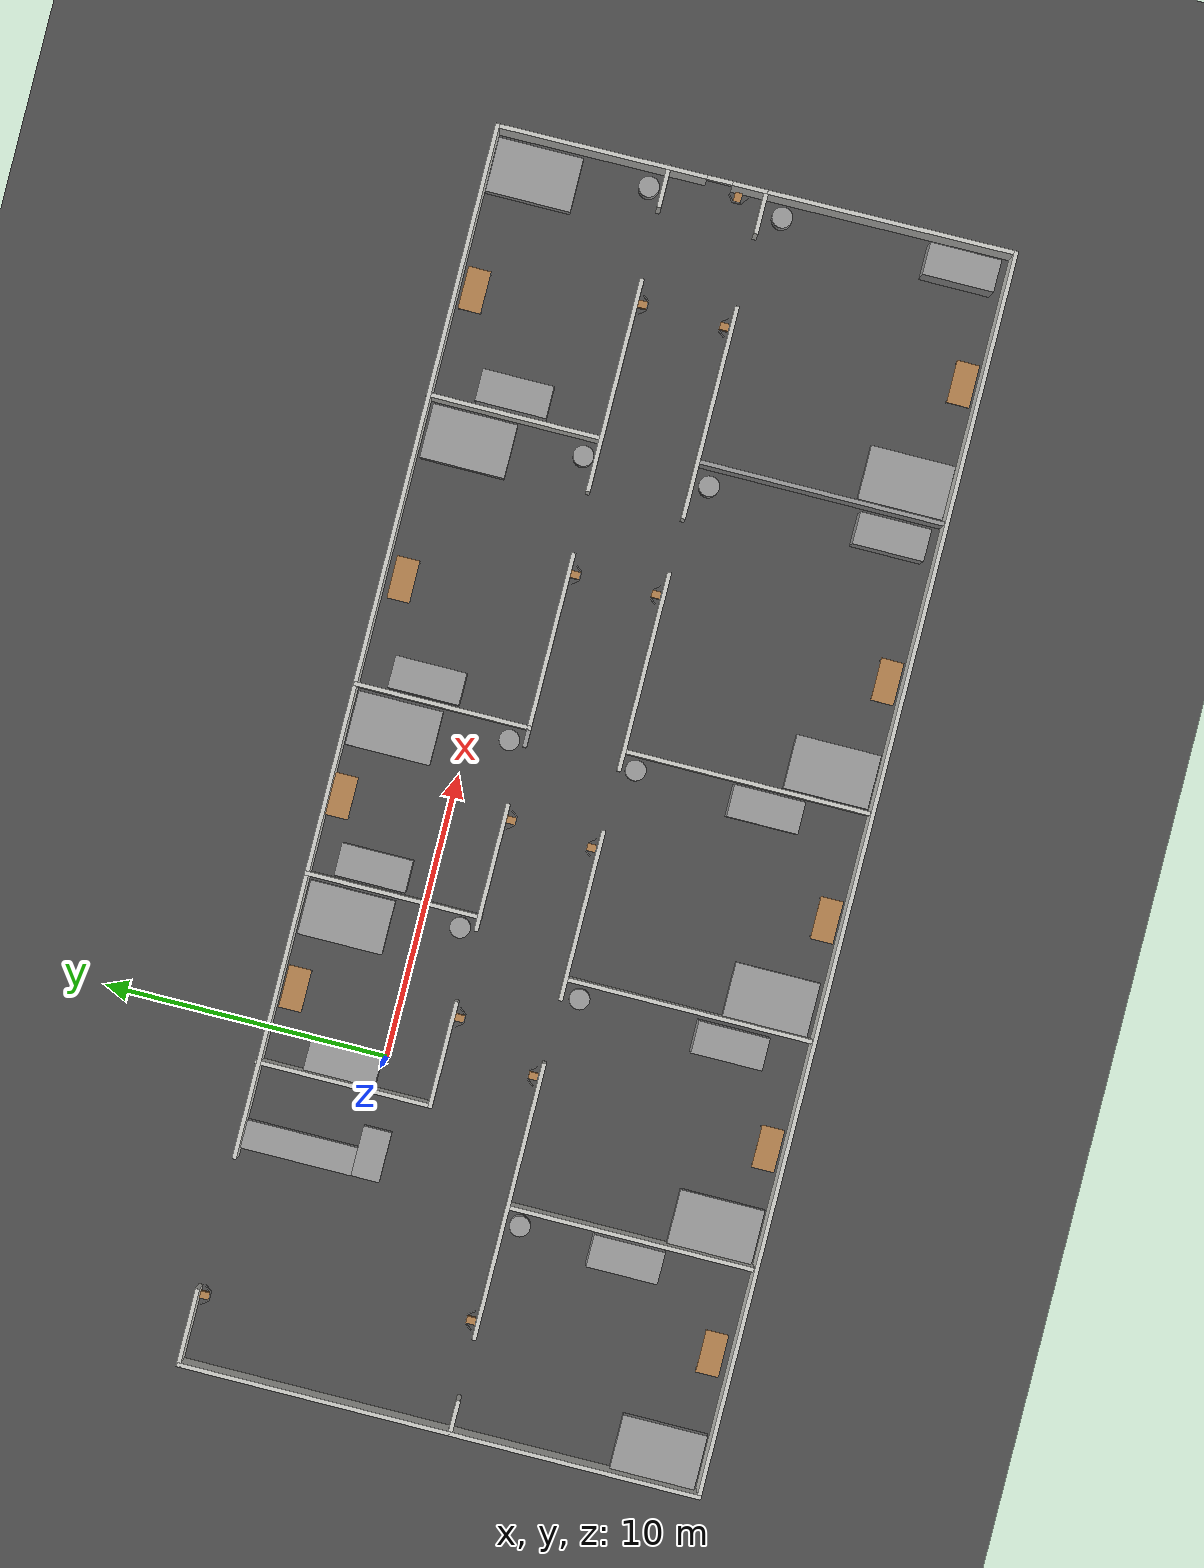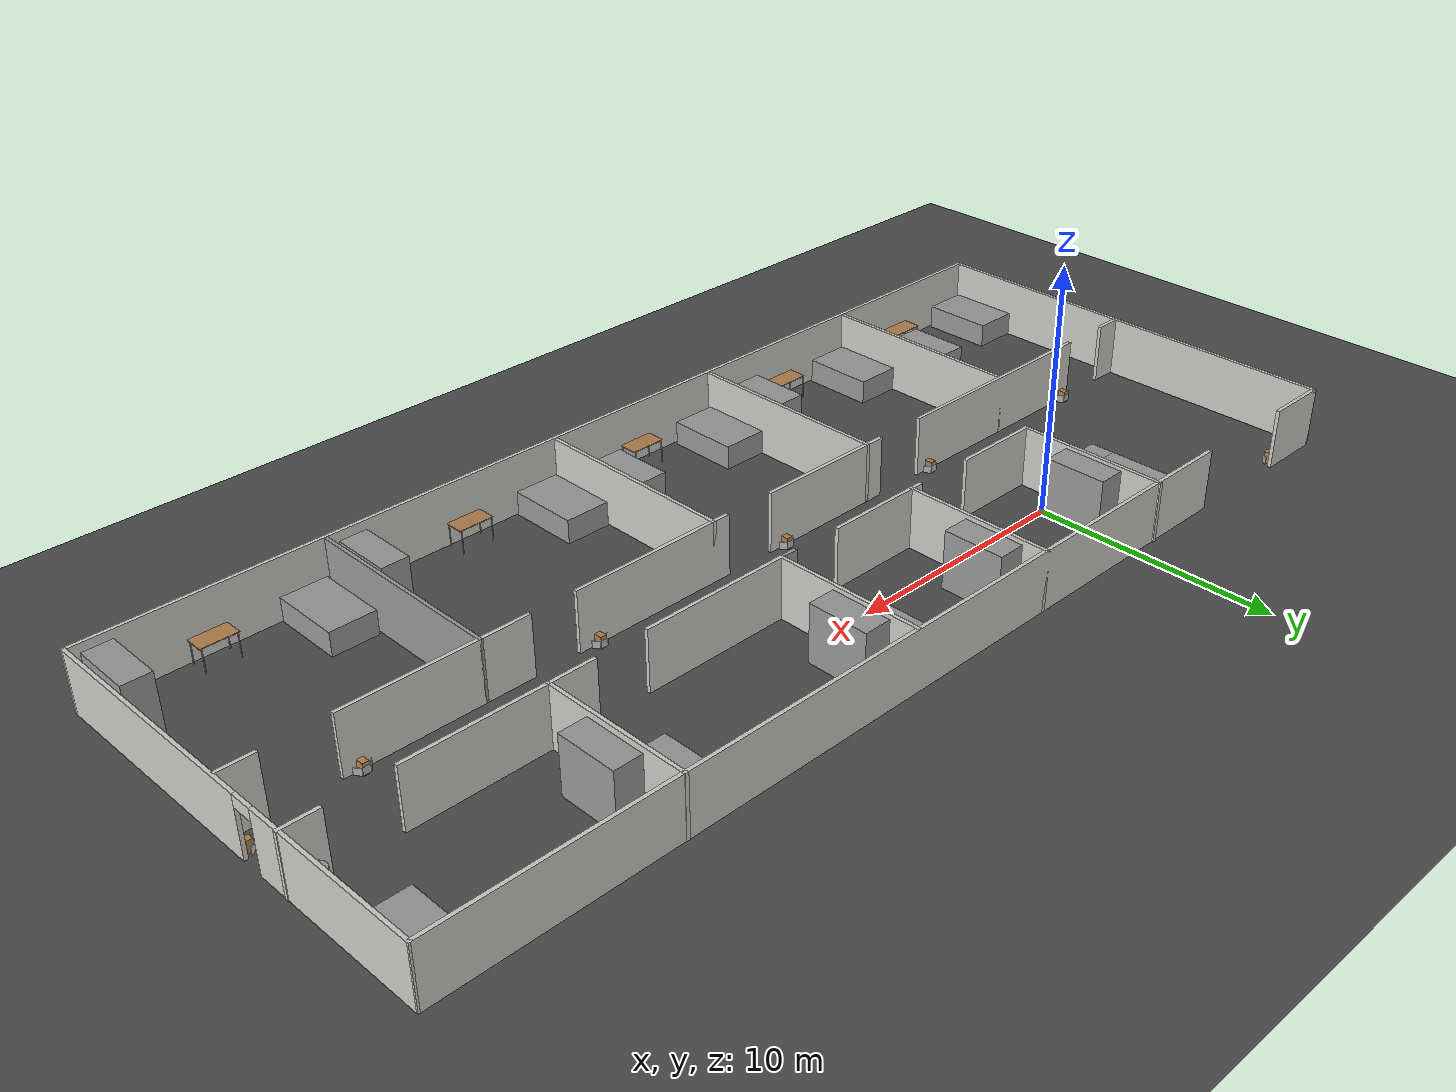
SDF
<sdf version="1.6">
 <world name="default">
  <light name="sun" type="directional">
   <pose>0 0 10 0 -0 0</pose>
   <diffuse>0.8 0.8 0.8 1</diffuse>
   <specular>0.2 0.2 0.2 1</specular>
   <attenuation>
    <range>1000</range>
    <constant>0.9</constant>
    <linear>0.01</linear>
    <quadratic>0.001</quadratic>
   </attenuation>
   <direction>-0.5 0.1 -0.9</direction>
  </light>
  <model name="ground_plane">
   <static>1</static>
   <link name="link">
    <collision name="collision">
     <geometry><plane><normal>0 0 1</normal><size>100 100</size></plane></geometry>
     <surface><friction><ode><mu>100</mu><mu2>50</mu2></ode></friction></surface>
    </collision>
    <visual name="visual">
     <cast_shadows>0</cast_shadows>
     <geometry><plane><normal>0 0 1</normal><size>100 100</size></plane></geometry>
     <material>
      <script><uri>file://media/materials/scripts/gazebo.material</uri><name>Gazebo/DarkGrey</name></script>
     </material>
    </visual>
   </link>
  </model>
  <gravity>0 0 -9.8</gravity>
  <magnetic_field>6e-06 2.3e-05 -4.2e-05</magnetic_field>
  <atmosphere type="adiabatic"/>
  <physics name="default_physics" default="0" type="ode">
   <max_step_size>0.001</max_step_size>
   <real_time_factor>1</real_time_factor>
   <real_time_update_rate>1000</real_time_update_rate>
  </physics>
  <scene><ambient>0.4 0.4 0.4 1</ambient><background>0.7 0.7 0.7 1</background><shadows>1</shadows></scene>
  <spherical_coordinates>
   <surface_model>EARTH_WGS84</surface_model>
   <latitude_deg>0</latitude_deg>
   <longitude_deg>0</longitude_deg>
   <elevation>0</elevation>
   <heading_deg>0</heading_deg>
  </spherical_coordinates>
  <model name="hospital_base">
   <pose>10.0746 -4.90069 0 0 -0 0</pose>
   <link name="Wall_0">
    <collision name="Wall_0_Collision">
     <geometry><box><size>2.75 0.15 2.5</size></box></geometry>
     <pose>0 0 1.25 0 -0 0</pose>
    </collision>
    <visual name="Wall_0_Visual">
     <pose>0 0 1.25 0 -0 0</pose>
     <geometry><box><size>2.75 0.15 2.5</size></box></geometry>
     <material>
      <script><uri>file://media/materials/scripts/gazebo.material</uri><name>Gazebo/CeilingTiled</name></script>
      <ambient>1 1 1 1</ambient>
     </material>
     <meta><layer>0</layer></meta>
    </visual>
    <pose>-20.6253 9.1753 0 0 -0 0</pose>
   </link>
   <link name="Wall_10">
    <collision name="Wall_10_Collision">
     <geometry><box><size>3.75 0.15 2.5</size></box></geometry>
     <pose>0 0 1.25 0 -0 0</pose>
    </collision>
    <visual name="Wall_10_Visual">
     <pose>0 0 1.25 0 -0 0</pose>
     <geometry><box><size>3.75 0.15 2.5</size></box></geometry>
     <material>
      <script><uri>file://media/materials/scripts/gazebo.material</uri><name>Gazebo/CeilingTiled</name></script>
      <ambient>1 1 1 1</ambient>
     </material>
     <meta><layer>0</layer></meta>
    </visual>
    <pose>-9.4395 3.0224 0 0 -0 0</pose>
   </link>
   <link name="Wall_12">
    <collision name="Wall_12_Collision">
     <geometry><box><size>4.5 0.15 2.5</size></box></geometry>
     <pose>0 0 1.25 0 -0 0</pose>
    </collision>
    <visual name="Wall_12_Visual">
     <pose>0 0 1.25 0 -0 0</pose>
     <geometry><box><size>4.5 0.15 2.5</size></box></geometry>
     <material>
      <script><uri>file://media/materials/scripts/gazebo.material</uri><name>Gazebo/CeilingTiled</name></script>
      <ambient>1 1 1 1</ambient>
     </material>
     <meta><layer>0</layer></meta>
    </visual>
    <pose>-2.8223 2.986 0 0 -0 0</pose>
   </link>
   <link name="Wall_14">
    <collision name="Wall_14_Collision">
     <geometry><box><size>6.25 0.15 2.5</size></box></geometry>
     <pose>0 0 1.25 0 -0 0</pose>
    </collision>
    <visual name="Wall_14_Visual">
     <pose>0 0 1.25 0 -0 0</pose>
     <geometry><box><size>6.25 0.15 2.5</size></box></geometry>
     <material>
      <script><uri>file://media/materials/scripts/gazebo.material</uri><name>Gazebo/CeilingTiled</name></script>
      <ambient>1 1 1 1</ambient>
     </material>
     <meta><layer>0</layer></meta>
    </visual>
    <pose>-4.5741 6.0195 0 0 -0 -1.5708</pose>
   </link>
   <link name="Wall_16">
    <collision name="Wall_16_Collision">
     <geometry><box><size>0.75 0.15 2.5</size></box></geometry>
     <pose>0 0 1.25 0 -0 0</pose>
    </collision>
    <visual name="Wall_16_Visual">
     <pose>0 0 1.25 0 -0 0</pose>
     <geometry><box><size>0.75 0.15 2.5</size></box></geometry>
     <material>
      <script><uri>file://media/materials/scripts/gazebo.material</uri><name>Gazebo/Grey</name></script>
      <ambient>1 1 1 1</ambient>
     </material>
     <meta><layer>0</layer></meta>
    </visual>
    <pose>1.8094 2.9331 0 0 -0 0</pose>
   </link>
   <link name="Wall_17">
    <collision name="Wall_17_Collision">
     <geometry><box><size>6.25 0.15 2.5</size></box></geometry>
     <pose>0 0 1.25 0 -0 0</pose>
    </collision>
    <visual name="Wall_17_Visual">
     <pose>0 0 1.25 0 -0 0</pose>
     <geometry><box><size>6.25 0.15 2.5</size></box></geometry>
     <material>
      <script><uri>file://media/materials/scripts/gazebo.material</uri><name>Gazebo/CeilingTiled</name></script>
      <ambient>1 1 1 1</ambient>
     </material>
     <meta><layer>0</layer></meta>
    </visual>
    <pose>2.1094 5.9831 0 0 -0 1.5708</pose>
   </link>
   <link name="Wall_19">
    <collision name="Wall_19_Collision">
     <geometry><box><size>6.25 0.15 2.5</size></box></geometry>
     <pose>0 0 1.25 0 -0 0</pose>
    </collision>
    <visual name="Wall_19_Visual">
     <pose>0 0 1.25 0 -0 0</pose>
     <geometry><box><size>6.25 0.15 2.5</size></box></geometry>
     <material>
      <script><uri>file://media/materials/scripts/gazebo.material</uri><name>Gazebo/CeilingTiled</name></script>
      <ambient>1 1 1 1</ambient>
     </material>
     <meta><layer>0</layer></meta>
    </visual>
    <pose>5.1594 2.9331 0 0 -0 0</pose>
   </link>
   <link name="Wall_2">
    <collision name="Wall_2_Collision">
     <geometry><box><size>36.5 0.15 2.5</size></box></geometry>
     <pose>0 0 1.25 0 -0 0</pose>
    </collision>
    <visual name="Wall_2_Visual">
     <pose>0 0 1.25 0 -0 0</pose>
     <geometry><box><size>36.5 0.15 2.5</size></box></geometry>
     <material>
      <script><uri>file://media/materials/scripts/gazebo.material</uri><name>Gazebo/CeilingTiled</name></script>
      <ambient>1 1 1 1</ambient>
     </material>
     <meta><layer>0</layer></meta>
    </visual>
    <pose>3.6028 9.0695 0 0 -0 0</pose>
   </link>
   <link name="Wall_23">
    <collision name="Wall_23_Collision">
     <geometry><box><size>7.5 0.15 2.5</size></box></geometry>
     <pose>0 0 1.25 0 -0 0</pose>
    </collision>
    <visual name="Wall_23_Visual">
     <pose>0 0 1.25 0 -0 0</pose>
     <geometry><box><size>7.5 0.15 2.5</size></box></geometry>
     <material>
      <script><uri>file://media/materials/scripts/gazebo.material</uri><name>Gazebo/CeilingTiled</name></script>
      <ambient>1 1 1 1</ambient>
     </material>
     <meta><layer>0</layer></meta>
    </visual>
    <pose>14.1774 2.986 0 0 -0 0</pose>
   </link>
   <link name="Wall_25">
    <collision name="Wall_25_Collision">
     <geometry><box><size>1.5 0.15 2.5</size></box></geometry>
     <pose>0 0 1.25 0 -0 0</pose>
    </collision>
    <visual name="Wall_25_Visual">
     <pose>0 0 1.25 0 -0 0</pose>
     <geometry><box><size>1.5 0.15 2.5</size></box></geometry>
     <material>
      <script><uri>file://media/materials/scripts/gazebo.material</uri><name>Gazebo/CeilingTiled</name></script>
      <ambient>1 1 1 1</ambient>
     </material>
     <meta><layer>0</layer></meta>
    </visual>
    <pose>21.1755 3.0389 0 0 -0 0</pose>
   </link>
   <link name="Wall_27">
    <collision name="Wall_27_Collision">
     <geometry><box><size>6.25 0.15 2.5</size></box></geometry>
     <pose>0 0 1.25 0 -0 0</pose>
    </collision>
    <visual name="Wall_27_Visual">
     <pose>0 0 1.25 0 -0 0</pose>
     <geometry><box><size>6.25 0.15 2.5</size></box></geometry>
     <material>
      <script><uri>file://media/materials/scripts/gazebo.material</uri><name>Gazebo/CeilingTiled</name></script>
      <ambient>1 1 1 1</ambient>
     </material>
     <meta><layer>0</layer></meta>
    </visual>
    <pose>12.301 6.036 0 0 -0 1.5708</pose>
   </link>
   <link name="Wall_29">
    <collision name="Wall_29_Collision">
     <geometry><box><size>1.25 0.15 2.5</size></box></geometry>
     <pose>0 0 1.25 0 -0 0</pose>
    </collision>
    <visual name="Wall_29_Visual">
     <pose>0 0 1.25 0 -0 0</pose>
     <geometry><box><size>1.25 0.15 2.5</size></box></geometry>
     <material>
      <script><uri>file://media/materials/scripts/gazebo.material</uri><name>Gazebo/CeilingTiled</name></script>
      <ambient>1 1 1 1</ambient>
     </material>
     <meta><layer>0</layer></meta>
    </visual>
    <pose>-21.3753 -0.3996 0 0 -0 0</pose>
   </link>
   <link name="Wall_31">
    <collision name="Wall_31_Collision">
     <geometry><box><size>9.75 0.15 2.5</size></box></geometry>
     <pose>0 0 1.25 0 -0 0</pose>
    </collision>
    <visual name="Wall_31_Visual">
     <pose>0 0 1.25 0 -0 0</pose>
     <geometry><box><size>9.75 0.15 2.5</size></box></geometry>
     <material>
      <script><uri>file://media/materials/scripts/gazebo.material</uri><name>Gazebo/CeilingTiled</name></script>
      <ambient>1 1 1 1</ambient>
     </material>
     <meta><layer>0</layer></meta>
    </visual>
    <pose>-13.7397 -0.3996 0 0 -0 0</pose>
   </link>
   <link name="Wall_33">
    <collision name="Wall_33_Collision">
     <geometry><box><size>6 0.15 2.5</size></box></geometry>
     <pose>0 0 1.25 0 -0 0</pose>
    </collision>
    <visual name="Wall_33_Visual">
     <pose>0 0 1.25 0 -0 0</pose>
     <geometry><box><size>6 0.15 2.5</size></box></geometry>
     <material>
      <script><uri>file://media/materials/scripts/gazebo.material</uri><name>Gazebo/CeilingTiled</name></script>
      <ambient>1 1 1 1</ambient>
     </material>
     <meta><layer>0</layer></meta>
    </visual>
    <pose>-3.6593 -0.3996 0 0 -0 0</pose>
   </link>
   <link name="Wall_35">
    <collision name="Wall_35_Collision">
     <geometry><box><size>7 0.15 2.5</size></box></geometry>
     <pose>0 0 1.25 0 -0 0</pose>
    </collision>
    <visual name="Wall_35_Visual">
     <pose>0 0 1.25 0 -0 0</pose>
     <geometry><box><size>7 0.15 2.5</size></box></geometry>
     <material>
      <script><uri>file://media/materials/scripts/gazebo.material</uri><name>Gazebo/CeilingTiled</name></script>
      <ambient>1 1 1 1</ambient>
     </material>
     <meta><layer>0</layer></meta>
    </visual>
    <pose>4.9344 -0.3996 0 0 -0 0</pose>
   </link>
   <link name="Wall_37">
    <collision name="Wall_37_Collision">
     <geometry><box><size>7.5 0.15 2.5</size></box></geometry>
     <pose>0 0 1.25 0 -0 0</pose>
    </collision>
    <visual name="Wall_37_Visual">
     <pose>0 0 1.25 0 -0 0</pose>
     <geometry><box><size>7.5 0.15 2.5</size></box></geometry>
     <material>
      <script><uri>file://media/materials/scripts/gazebo.material</uri><name>Gazebo/CeilingTiled</name></script>
      <ambient>1 1 1 1</ambient>
     </material>
     <meta><layer>0</layer></meta>
    </visual>
    <pose>14.0716 -0.3996 0 0 -0 0</pose>
   </link>
   <link name="Wall_39">
    <collision name="Wall_39_Collision">
     <geometry><box><size>1.5 0.15 2.5</size></box></geometry>
     <pose>0 0 1.25 0 -0 0</pose>
    </collision>
    <visual name="Wall_39_Visual">
     <pose>0 0 1.25 0 -0 0</pose>
     <geometry><box><size>1.5 0.15 2.5</size></box></geometry>
     <material>
      <script><uri>file://media/materials/scripts/gazebo.material</uri><name>Gazebo/CeilingTiled</name></script>
      <ambient>1 1 1 1</ambient>
     </material>
     <meta><layer>0</layer></meta>
    </visual>
    <pose>21.1226 -0.3996 0 0 -0 0</pose>
   </link>
   <link name="Wall_41">
    <collision name="Wall_41_Collision">
     <geometry><box><size>8.75 0.15 2.5</size></box></geometry>
     <pose>0 0 1.25 0 -0 0</pose>
    </collision>
    <visual name="Wall_41_Visual">
     <pose>0 0 1.25 0 -0 0</pose>
     <geometry><box><size>8.75 0.15 2.5</size></box></geometry>
     <material>
      <script><uri>file://media/materials/scripts/gazebo.material</uri><name>Gazebo/Grey</name></script>
      <ambient>1 1 1 1</ambient>
     </material>
     <meta><layer>0</layer></meta>
    </visual>
    <pose>12.3539 -4.6996 0 0 -0 -1.5708</pose>
   </link>
   <link name="Wall_43">
    <collision name="Wall_43_Collision">
     <geometry><box><size>8.75 0.15 2.5</size></box></geometry>
     <pose>0 0 1.25 0 -0 0</pose>
    </collision>
    <visual name="Wall_43_Visual">
     <pose>0 0 1.25 0 -0 0</pose>
     <geometry><box><size>8.75 0.15 2.5</size></box></geometry>
     <material>
      <script><uri>file://media/materials/scripts/gazebo.material</uri><name>Gazebo/CeilingTiled</name></script>
      <ambient>1 1 1 1</ambient>
     </material>
     <meta><layer>0</layer></meta>
    </visual>
    <pose>2.1442 -4.6996 0 0 -0 -1.5708</pose>
   </link>
   <link name="Wall_45">
    <collision name="Wall_45_Collision">
     <geometry><box><size>8.75 0.15 2.5</size></box></geometry>
     <pose>0 0 1.25 0 -0 0</pose>
    </collision>
    <visual name="Wall_45_Visual">
     <pose>0 0 1.25 0 -0 0</pose>
     <geometry><box><size>8.75 0.15 2.5</size></box></geometry>
     <material>
      <script><uri>file://media/materials/scripts/gazebo.material</uri><name>Gazebo/CeilingTiled</name></script>
      <ambient>1 1 1 1</ambient>
     </material>
     <meta><layer>0</layer></meta>
    </visual>
    <pose>-5.8966 -4.6996 0 0 -0 -1.5708</pose>
   </link>
   <link name="Wall_47">
    <collision name="Wall_47_Collision">
     <geometry><box><size>8.75 0.15 2.5</size></box></geometry>
     <pose>0 0 1.25 0 -0 0</pose>
    </collision>
    <visual name="Wall_47_Visual">
     <pose>0 0 1.25 0 -0 0</pose>
     <geometry><box><size>8.75 0.15 2.5</size></box></geometry>
     <material>
      <script><uri>file://media/materials/scripts/gazebo.material</uri><name>Gazebo/CeilingTiled</name></script>
      <ambient>1 1 1 1</ambient>
     </material>
     <meta><layer>0</layer></meta>
    </visual>
    <pose>-13.9374 -4.6996 0 0 -0 -1.5708</pose>
   </link>
   <link name="Wall_5">
    <collision name="Wall_5_Collision">
     <geometry><box><size>18.5 0.15 2.5</size></box></geometry>
     <pose>0 0 1.25 0 -0 0</pose>
    </collision>
    <visual name="Wall_5_Visual">
     <pose>0 0 1.25 0 -0 0</pose>
     <geometry><box><size>18.5 0.15 2.5</size></box></geometry>
     <material>
      <script><uri>file://media/materials/scripts/gazebo.material</uri><name>Gazebo/CeilingTiled</name></script>
      <ambient>1 1 1 1</ambient>
     </material>
     <meta><layer>0</layer></meta>
    </visual>
    <pose>-21.9253 0.0003 0 0 -0 -1.5708</pose>
   </link>
   <link name="Wall_6">
    <collision name="Wall_6_Collision">
     <geometry><box><size>44 0.15 2.5</size></box></geometry>
     <pose>0 0 1.25 0 -0 0</pose>
    </collision>
    <visual name="Wall_6_Visual">
     <pose>0 0 1.25 0 -0 0</pose>
     <geometry><box><size>44 0.15 2.5</size></box></geometry>
     <material>
      <script><uri>file://media/materials/scripts/gazebo.material</uri><name>Gazebo/CeilingTiled</name></script>
      <ambient>1 1 1 1</ambient>
     </material>
     <meta><layer>0</layer></meta>
    </visual>
    <pose>-0.0003 -9.1747 0 0 -0 0</pose>
   </link>
   <link name="Wall_7">
    <pose>21.8513 -0.0526 0 0 -0 1.57885</pose>
    <visual name="Wall_7_Visual_0">
     <pose>-4.17652 0 1.25 0 -0 0</pose>
     <geometry><box><size>10.0418 0.15 2.5</size></box></geometry>
     <material>
      <script><uri>file://media/materials/scripts/gazebo.material</uri><name>Gazebo/CeilingTiled</name></script>
      <ambient>1 1 1 1</ambient>
     </material>
     <meta><layer>0</layer></meta>
    </visual>
    <collision name="Wall_7_Collision_0">
     <geometry><box><size>10.0418 0.15 2.5</size></box></geometry>
     <pose>-4.17652 0 1.25 0 -0 0</pose>
    </collision>
    <visual name="Wall_7_Visual_1">
     <pose>5.47088 0 1.25 0 -0 0</pose>
     <geometry><box><size>7.45303 0.15 2.5</size></box></geometry>
     <material>
      <script><uri>file://media/materials/scripts/gazebo.material</uri><name>Gazebo/CeilingTiled</name></script>
      <ambient>1 1 1 1</ambient>
     </material>
     <meta><layer>0</layer></meta>
    </visual>
    <collision name="Wall_7_Collision_1">
     <geometry><box><size>7.45303 0.15 2.5</size></box></geometry>
     <pose>5.47088 0 1.25 0 -0 0</pose>
    </collision>
    <visual name="Wall_7_Visual_2">
     <pose>1.29436 0 2.25 0 -0 0</pose>
     <geometry><box><size>0.9 0.15 0.5</size></box></geometry>
     <material>
      <script><uri>file://media/materials/scripts/gazebo.material</uri><name>Gazebo/CeilingTiled</name></script>
      <ambient>1 1 1 1</ambient>
     </material>
     <meta><layer>0</layer></meta>
    </visual>
    <collision name="Wall_7_Collision_2">
     <geometry><box><size>0.9 0.15 0.5</size></box></geometry>
     <pose>1.29436 0 2.25 0 -0 0</pose>
    </collision>
   </link>
   <link name="Wall_9">
    <collision name="Wall_9_Collision">
     <geometry><box><size>6.25 0.15 2.5</size></box></geometry>
     <pose>0 0 1.25 0 -0 0</pose>
    </collision>
    <visual name="Wall_9_Visual">
     <pose>0 0 1.25 0 -0 0</pose>
     <geometry><box><size>6.25 0.15 2.5</size></box></geometry>
     <material>
      <script><uri>file://media/materials/scripts/gazebo.material</uri><name>Gazebo/CeilingTiled</name></script>
      <ambient>1 1 1 1</ambient>
     </material>
     <meta><layer>0</layer></meta>
    </visual>
    <pose>-11.2395 6.0724 0 0 -0 -1.5708</pose>
   </link>
   <static>1</static>
  </model>
  <model name="table">
   <static>1</static>
   <link name="link">
    <collision name="surface">
     <pose>0 0 1 0 -0 0</pose>
     <geometry><box><size>1.5 0.8 0.03</size></box></geometry>
     <surface><friction><ode><mu>0.6</mu><mu2>0.6</mu2></ode></friction></surface>
    </collision>
    <visual name="visual1">
     <pose>0 0 1 0 -0 0</pose>
     <geometry><box><size>1.5 0.8 0.03</size></box></geometry>
     <material>
      <script><uri>file://media/materials/scripts/gazebo.material</uri><name>Gazebo/Wood</name></script>
     </material>
    </visual>
    <collision name="front_left_leg">
     <pose>0.68 0.38 0.5 0 -0 0</pose>
     <geometry><cylinder><radius>0.02</radius><length>1</length></cylinder></geometry>
    </collision>
    <visual name="front_left_leg">
     <pose>0.68 0.38 0.5 0 -0 0</pose>
     <geometry><cylinder><radius>0.02</radius><length>1</length></cylinder></geometry>
     <material>
      <script><uri>file://media/materials/scripts/gazebo.material</uri><name>Gazebo/Grey</name></script>
     </material>
    </visual>
    <collision name="front_right_leg">
     <pose>0.68 -0.38 0.5 0 -0 0</pose>
     <geometry><cylinder><radius>0.02</radius><length>1</length></cylinder></geometry>
    </collision>
    <visual name="front_right_leg">
     <pose>0.68 -0.38 0.5 0 -0 0</pose>
     <geometry><cylinder><radius>0.02</radius><length>1</length></cylinder></geometry>
     <material>
      <script><uri>file://media/materials/scripts/gazebo.material</uri><name>Gazebo/Grey</name></script>
     </material>
    </visual>
    <collision name="back_right_leg">
     <pose>-0.68 -0.38 0.5 0 -0 0</pose>
     <geometry><cylinder><radius>0.02</radius><length>1</length></cylinder></geometry>
    </collision>
    <visual name="back_right_leg">
     <pose>-0.68 -0.38 0.5 0 -0 0</pose>
     <geometry><cylinder><radius>0.02</radius><length>1</length></cylinder></geometry>
     <material>
      <script><uri>file://media/materials/scripts/gazebo.material</uri><name>Gazebo/Grey</name></script>
     </material>
    </visual>
    <collision name="back_left_leg">
     <pose>-0.68 0.38 0.5 0 -0 0</pose>
     <geometry><cylinder><radius>0.02</radius><length>1</length></cylinder></geometry>
    </collision>
    <visual name="back_left_leg">
     <pose>-0.68 0.38 0.5 0 -0 0</pose>
     <geometry><cylinder><radius>0.02</radius><length>1</length></cylinder></geometry>
     <material>
      <script><uri>file://media/materials/scripts/gazebo.material</uri><name>Gazebo/Grey</name></script>
     </material>
    </visual>
   </link>
   <pose>-7.07906 -13.3673 0 0 -0 0</pose>
  </model>
  <model name="unit_box_1_clone">
   <pose>-2.83505 -12.4182 0.5 0 1e-06 1e-06</pose>
   <link name="link">
    <inertial>
     <mass>1</mass>
     <inertia>
      <ixx>0.166667</ixx>
      <ixy>0</ixy>
      <ixz>0</ixz>
      <iyy>0.166667</iyy>
      <iyz>0</iyz>
      <izz>0.166667</izz>
     </inertia>
    </inertial>
    <collision name="collision"><geometry><box><size>1.90543 2.99439 1</size></box></geometry></collision>
    <visual name="visual">
     <geometry><box><size>1.90543 2.99439 1</size></box></geometry>
     <material>
      <script><name>Gazebo/Grey</name><uri>file://media/materials/scripts/gazebo.material</uri></script>
     </material>
    </visual>
   </link>
  </model>
  <model name="unit_box_1_clone_0">
   <pose>5.20571 -12.3359 0.499826 -0.000116 -0 -2e-06</pose>
   <link name="link">
    <inertial>
     <mass>1</mass>
     <inertia>
      <ixx>0.166667</ixx>
      <ixy>0</ixy>
      <ixz>0</ixz>
      <iyy>0.166667</iyy>
      <iyz>0</iyz>
      <izz>0.166667</izz>
     </inertia>
    </inertial>
    <collision name="collision"><geometry><box><size>1.90543 2.99439 1</size></box></geometry></collision>
    <visual name="visual">
     <geometry><box><size>1.90543 2.99439 1</size></box></geometry>
     <material>
      <script><name>Gazebo/Grey</name><uri>file://media/materials/scripts/gazebo.material</uri></script>
     </material>
    </visual>
   </link>
  </model>
  <model name="unit_box_1_clone_1">
   <pose>13.3078 -12.4311 0.499989 -0 -1.2e-05 -6e-06</pose>
   <link name="link">
    <inertial>
     <mass>1</mass>
     <inertia>
      <ixx>0.166667</ixx>
      <ixy>0</ixy>
      <ixz>0</ixz>
      <iyy>0.166667</iyy>
      <iyz>0</iyz>
      <izz>0.166667</izz>
     </inertia>
    </inertial>
    <collision name="collision"><geometry><box><size>1.90543 2.99439 1</size></box></geometry></collision>
    <visual name="visual">
     <geometry><box><size>1.90543 2.99439 1</size></box></geometry>
     <material>
      <script><name>Gazebo/Grey</name><uri>file://media/materials/scripts/gazebo.material</uri></script>
     </material>
    </visual>
   </link>
  </model>
  <model name="unit_box_1_clone_2">
   <pose>23.5687 -12.4542 0.499989 0 -1.2e-05 -0.000269</pose>
   <link name="link">
    <inertial>
     <mass>1</mass>
     <inertia>
      <ixx>0.166667</ixx>
      <ixy>0</ixy>
      <ixz>0</ixz>
      <iyy>0.166667</iyy>
      <iyz>0</iyz>
      <izz>0.166667</izz>
     </inertia>
    </inertial>
    <collision name="collision"><geometry><box><size>1.90543 2.99439 1</size></box></geometry></collision>
    <visual name="visual">
     <geometry><box><size>1.90543 2.99439 1</size></box></geometry>
     <material>
      <script><name>Gazebo/Grey</name><uri>file://media/materials/scripts/gazebo.material</uri></script>
     </material>
    </visual>
   </link>
  </model>
  <model name="unit_box_1_clone_3">
   <pose>30.6663 2.55489 0.499989 0 1.2e-05 3.8e-05</pose>
   <link name="link">
    <inertial>
     <mass>1</mass>
     <inertia>
      <ixx>0.166667</ixx>
      <ixy>0</ixy>
      <ixz>0</ixz>
      <iyy>0.166667</iyy>
      <iyz>0</iyz>
      <izz>0.166667</izz>
     </inertia>
    </inertial>
    <collision name="collision"><geometry><box><size>1.90543 2.99439 1</size></box></geometry></collision>
    <visual name="visual">
     <geometry><box><size>1.90543 2.99439 1</size></box></geometry>
     <material>
      <script><name>Gazebo/Grey</name><uri>file://media/materials/scripts/gazebo.material</uri></script>
     </material>
    </visual>
   </link>
  </model>
  <model name="unit_box_1_clone_4">
   <pose>21.2387 2.48779 0.499989 0 -1.2e-05 -0.000153</pose>
   <link name="link">
    <inertial>
     <mass>1</mass>
     <inertia>
      <ixx>0.166667</ixx>
      <ixy>0</ixy>
      <ixz>0</ixz>
      <iyy>0.166667</iyy>
      <iyz>0</iyz>
      <izz>0.166667</izz>
     </inertia>
    </inertial>
    <collision name="collision"><geometry><box><size>1.90543 2.99439 1</size></box></geometry></collision>
    <visual name="visual">
     <geometry><box><size>1.90543 2.99439 1</size></box></geometry>
     <material>
      <script><name>Gazebo/Grey</name><uri>file://media/materials/scripts/gazebo.material</uri></script>
     </material>
    </visual>
   </link>
  </model>
  <model name="unit_box_1_clone_5">
   <pose>4.33951 2.52234 0.499989 0 1.2e-05 -0.000106</pose>
   <link name="link">
    <inertial>
     <mass>1</mass>
     <inertia>
      <ixx>0.166667</ixx>
      <ixy>0</ixy>
      <ixz>0</ixz>
      <iyy>0.166667</iyy>
      <iyz>0</iyz>
      <izz>0.166667</izz>
     </inertia>
    </inertial>
    <collision name="collision"><geometry><box><size>1.90543 2.99439 1</size></box></geometry></collision>
    <visual name="visual">
     <geometry><box><size>1.90543 2.99439 1</size></box></geometry>
     <material>
      <script><name>Gazebo/Grey</name><uri>file://media/materials/scripts/gazebo.material</uri></script>
     </material>
    </visual>
   </link>
  </model>
  <model name="unit_box_1_clone_6">
   <pose>11.0495 2.53281 0.499989 0 1.2e-05 -0.000166</pose>
   <link name="link">
    <inertial>
     <mass>1</mass>
     <inertia>
      <ixx>0.166667</ixx>
      <ixy>0</ixy>
      <ixz>0</ixz>
      <iyy>0.166667</iyy>
      <iyz>0</iyz>
      <izz>0.166667</izz>
     </inertia>
    </inertial>
    <collision name="collision"><geometry><box><size>1.90543 2.99439 1</size></box></geometry></collision>
    <visual name="visual">
     <geometry><box><size>1.90543 2.99439 1</size></box></geometry>
     <material>
      <script><name>Gazebo/Grey</name><uri>file://media/materials/scripts/gazebo.material</uri></script>
     </material>
    </visual>
   </link>
  </model>
  <model name="unit_cylinder_clone">
   <pose>3.5861 -5.9388 0.499992 0 -0 0</pose>
   <link name="link">
    <inertial>
     <mass>1</mass>
     <inertia><ixx>0.145833</ixx><ixy>0</ixy><ixz>0</ixz><iyy>0.145833</iyy><iyz>0</iyz><izz>0.125</izz></inertia>
    </inertial>
    <collision name="collision">
     <geometry><cylinder><radius>0.361483</radius><length>1</length></cylinder></geometry>
    </collision>
    <visual name="visual">
     <geometry><cylinder><radius>0.361483</radius><length>1</length></cylinder></geometry>
     <material>
      <script><name>Gazebo/Grey</name><uri>file://media/materials/scripts/gazebo.material</uri></script>
     </material>
    </visual>
   </link>
  </model>
  <model name="unit_cylinder_clone_0">
   <pose>11.6867 -5.87007 0.499992 0 -0 0</pose>
   <link name="link">
    <inertial>
     <mass>1</mass>
     <inertia><ixx>0.145833</ixx><ixy>0</ixy><ixz>0</ixz><iyy>0.145833</iyy><iyz>0</iyz><izz>0.125</izz></inertia>
    </inertial>
    <collision name="collision">
     <geometry><cylinder><radius>0.361483</radius><length>1</length></cylinder></geometry>
    </collision>
    <visual name="visual">
     <geometry><cylinder><radius>0.361483</radius><length>1</length></cylinder></geometry>
     <material>
      <script><name>Gazebo/Grey</name><uri>file://media/materials/scripts/gazebo.material</uri></script>
     </material>
    </visual>
   </link>
  </model>
  <model name="unit_cylinder_clone_1">
   <pose>21.7711 -5.90074 0.499992 0 -0 0</pose>
   <link name="link">
    <inertial>
     <mass>1</mass>
     <inertia><ixx>0.145833</ixx><ixy>0</ixy><ixz>0</ixz><iyy>0.145833</iyy><iyz>0</iyz><izz>0.125</izz></inertia>
    </inertial>
    <collision name="collision">
     <geometry><cylinder><radius>0.361483</radius><length>1</length></cylinder></geometry>
    </collision>
    <visual name="visual">
     <geometry><cylinder><radius>0.361483</radius><length>1</length></cylinder></geometry>
     <material>
      <script><name>Gazebo/Grey</name><uri>file://media/materials/scripts/gazebo.material</uri></script>
     </material>
    </visual>
   </link>
  </model>
  <model name="unit_cylinder_clone_2">
   <pose>31.3402 -6.05699 0.499992 0 0 -0.001355</pose>
   <link name="link">
    <inertial>
     <mass>1</mass>
     <inertia><ixx>0.145833</ixx><ixy>0</ixy><ixz>0</ixz><iyy>0.145833</iyy><iyz>0</iyz><izz>0.125</izz></inertia>
    </inertial>
    <collision name="collision">
     <geometry><cylinder><radius>0.361483</radius><length>1</length></cylinder></geometry>
    </collision>
    <visual name="visual">
     <geometry><cylinder><radius>0.361483</radius><length>1</length></cylinder></geometry>
     <material>
      <script><name>Gazebo/Grey</name><uri>file://media/materials/scripts/gazebo.material</uri></script>
     </material>
    </visual>
   </link>
  </model>
  <model name="unit_box_2_clone">
   <pose>3.35905 -11.3146 1.1904 4e-06 -1e-06 8.5e-05</pose>
   <link name="link">
    <inertial>
     <mass>1</mass>
     <inertia>
      <ixx>0.166667</ixx>
      <ixy>0</ixy>
      <ixz>0</ixz>
      <iyy>0.166667</iyy>
      <iyz>0</iyz>
      <izz>0.166667</izz>
     </inertia>
    </inertial>
    <collision name="collision"><geometry><box><size>1.13758 2.51147 2.38082</size></box></geometry></collision>
    <visual name="visual">
     <geometry><box><size>1.13758 2.51147 2.38082</size></box></geometry>
     <material>
      <script><name>Gazebo/Grey</name><uri>file://media/materials/scripts/gazebo.material</uri></script>
     </material>
    </visual>
   </link>
  </model>
  <model name="unit_box_2_clone_0">
   <pose>11.4893 -10.5003 1.19041 0 -0 8.2e-05</pose>
   <link name="link">
    <inertial>
     <mass>1</mass>
     <inertia>
      <ixx>0.166667</ixx>
      <ixy>0</ixy>
      <ixz>0</ixz>
      <iyy>0.166667</iyy>
      <iyz>0</iyz>
      <izz>0.166667</izz>
     </inertia>
    </inertial>
    <collision name="collision"><geometry><box><size>1.13758 2.51147 2.38082</size></box></geometry></collision>
    <visual name="visual">
     <geometry><box><size>1.13758 2.51147 2.38082</size></box></geometry>
     <material>
      <script><name>Gazebo/Grey</name><uri>file://media/materials/scripts/gazebo.material</uri></script>
     </material>
    </visual>
   </link>
  </model>
  <model name="unit_box_2_clone_1">
   <pose>21.5822 -12.3633 1.1904 4e-06 -1e-06 8.5e-05</pose>
   <link name="link">
    <inertial>
     <mass>1</mass>
     <inertia>
      <ixx>0.166667</ixx>
      <ixy>0</ixy>
      <ixz>0</ixz>
      <iyy>0.166667</iyy>
      <iyz>0</iyz>
      <izz>0.166667</izz>
     </inertia>
    </inertial>
    <collision name="collision"><geometry><box><size>1.13758 2.51147 2.38082</size></box></geometry></collision>
    <visual name="visual">
     <geometry><box><size>1.13758 2.51147 2.38082</size></box></geometry>
     <material>
      <script><name>Gazebo/Grey</name><uri>file://media/materials/scripts/gazebo.material</uri></script>
     </material>
    </visual>
   </link>
  </model>
  <model name="unit_box_2_clone_2">
   <pose>31.0935 -12.4085 1.19041 0 -0 8.3e-05</pose>
   <link name="link">
    <inertial>
     <mass>1</mass>
     <inertia>
      <ixx>0.166667</ixx>
      <ixy>0</ixy>
      <ixz>0</ixz>
      <iyy>0.166667</iyy>
      <iyz>0</iyz>
      <izz>0.166667</izz>
     </inertia>
    </inertial>
    <collision name="collision"><geometry><box><size>1.13758 2.51147 2.38082</size></box></geometry></collision>
    <visual name="visual">
     <geometry><box><size>1.13758 2.51147 2.38082</size></box></geometry>
     <material>
      <script><name>Gazebo/Grey</name><uri>file://media/materials/scripts/gazebo.material</uri></script>
     </material>
    </visual>
   </link>
  </model>
  <model name="unit_box_2_clone_3">
   <pose>23.1302 1.34664 1.1904 4e-06 -1e-06 8.4e-05</pose>
   <link name="link">
    <inertial>
     <mass>1</mass>
     <inertia>
      <ixx>0.166667</ixx>
      <ixy>0</ixy>
      <ixz>0</ixz>
      <iyy>0.166667</iyy>
      <iyz>0</iyz>
      <izz>0.166667</izz>
     </inertia>
    </inertial>
    <collision name="collision"><geometry><box><size>1.13758 2.51147 2.38082</size></box></geometry></collision>
    <visual name="visual">
     <geometry><box><size>1.13758 2.51147 2.38082</size></box></geometry>
     <material>
      <script><name>Gazebo/Grey</name><uri>file://media/materials/scripts/gazebo.material</uri></script>
     </material>
    </visual>
   </link>
  </model>
  <model name="unit_box_2_clone_4">
   <pose>12.9009 1.81429 1.1904 4e-06 1e-06 8.3e-05</pose>
   <link name="link">
    <inertial>
     <mass>1</mass>
     <inertia>
      <ixx>0.166667</ixx>
      <ixy>0</ixy>
      <ixz>0</ixz>
      <iyy>0.166667</iyy>
      <iyz>0</iyz>
      <izz>0.166667</izz>
     </inertia>
    </inertial>
    <collision name="collision"><geometry><box><size>1.13758 2.51147 2.38082</size></box></geometry></collision>
    <visual name="visual">
     <geometry><box><size>1.13758 2.51147 2.38082</size></box></geometry>
     <material>
      <script><name>Gazebo/Grey</name><uri>file://media/materials/scripts/gazebo.material</uri></script>
     </material>
    </visual>
   </link>
  </model>
  <model name="unit_box_2_clone_5">
   <pose>6.23937 2.00477 1.19041 0 -0 8.3e-05</pose>
   <link name="link">
    <inertial>
     <mass>1</mass>
     <inertia>
      <ixx>0.166667</ixx>
      <ixy>0</ixy>
      <ixz>0</ixz>
      <iyy>0.166667</iyy>
      <iyz>0</iyz>
      <izz>0.166667</izz>
     </inertia>
    </inertial>
    <collision name="collision"><geometry><box><size>1.13758 2.51147 2.38082</size></box></geometry></collision>
    <visual name="visual">
     <geometry><box><size>1.13758 2.51147 2.38082</size></box></geometry>
     <material>
      <script><name>Gazebo/Grey</name><uri>file://media/materials/scripts/gazebo.material</uri></script>
     </material>
    </visual>
   </link>
  </model>
  <model name="unit_box_2_clone_6">
   <pose>-0.469652 1.38013 1.1904 4e-06 -1e-06 8.7e-05</pose>
   <link name="link">
    <inertial>
     <mass>1</mass>
     <inertia>
      <ixx>0.166667</ixx>
      <ixy>0</ixy>
      <ixz>0</ixz>
      <iyy>0.166667</iyy>
      <iyz>0</iyz>
      <izz>0.166667</izz>
     </inertia>
    </inertial>
    <collision name="collision"><geometry><box><size>1.13758 2.51147 2.38082</size></box></geometry></collision>
    <visual name="visual">
     <geometry><box><size>1.13758 2.51147 2.38082</size></box></geometry>
     <material>
      <script><name>Gazebo/Grey</name><uri>file://media/materials/scripts/gazebo.material</uri></script>
     </material>
    </visual>
   </link>
  </model>
  <model name="table_clone">
   <static>1</static>
   <link name="link">
    <collision name="surface">
     <pose>0 0 1 0 -0 0</pose>
     <geometry><box><size>1.5 0.8 0.03</size></box></geometry>
     <surface><friction><ode><mu>0.6</mu><mu2>0.6</mu2></ode></friction></surface>
    </collision>
    <visual name="visual1">
     <pose>0 0 1 0 -0 0</pose>
     <geometry><box><size>1.5 0.8 0.03</size></box></geometry>
     <material>
      <script><uri>file://media/materials/scripts/gazebo.material</uri><name>Gazebo/Wood</name></script>
     </material>
    </visual>
    <collision name="front_left_leg">
     <pose>0.68 0.38 0.5 0 -0 0</pose>
     <geometry><cylinder><radius>0.02</radius><length>1</length></cylinder></geometry>
    </collision>
    <visual name="front_left_leg">
     <pose>0.68 0.38 0.5 0 -0 0</pose>
     <geometry><cylinder><radius>0.02</radius><length>1</length></cylinder></geometry>
     <material>
      <script><uri>file://media/materials/scripts/gazebo.material</uri><name>Gazebo/Grey</name></script>
     </material>
    </visual>
    <collision name="front_right_leg">
     <pose>0.68 -0.38 0.5 0 -0 0</pose>
     <geometry><cylinder><radius>0.02</radius><length>1</length></cylinder></geometry>
    </collision>
    <visual name="front_right_leg">
     <pose>0.68 -0.38 0.5 0 -0 0</pose>
     <geometry><cylinder><radius>0.02</radius><length>1</length></cylinder></geometry>
     <material>
      <script><uri>file://media/materials/scripts/gazebo.material</uri><name>Gazebo/Grey</name></script>
     </material>
    </visual>
    <collision name="back_right_leg">
     <pose>-0.68 -0.38 0.5 0 -0 0</pose>
     <geometry><cylinder><radius>0.02</radius><length>1</length></cylinder></geometry>
    </collision>
    <visual name="back_right_leg">
     <pose>-0.68 -0.38 0.5 0 -0 0</pose>
     <geometry><cylinder><radius>0.02</radius><length>1</length></cylinder></geometry>
     <material>
      <script><uri>file://media/materials/scripts/gazebo.material</uri><name>Gazebo/Grey</name></script>
     </material>
    </visual>
    <collision name="back_left_leg">
     <pose>-0.68 0.38 0.5 0 -0 0</pose>
     <geometry><cylinder><radius>0.02</radius><length>1</length></cylinder></geometry>
    </collision>
    <visual name="back_left_leg">
     <pose>-0.68 0.38 0.5 0 -0 0</pose>
     <geometry><cylinder><radius>0.02</radius><length>1</length></cylinder></geometry>
     <material>
      <script><uri>file://media/materials/scripts/gazebo.material</uri><name>Gazebo/Grey</name></script>
     </material>
    </visual>
   </link>
   <pose>0.212931 -13.4896 0 0 -0 0</pose>
  </model>
  <model name="table_clone_0">
   <static>1</static>
   <link name="link">
    <collision name="surface">
     <pose>0 0 1 0 -0 0</pose>
     <geometry><box><size>1.5 0.8 0.03</size></box></geometry>
     <surface><friction><ode><mu>0.6</mu><mu2>0.6</mu2></ode></friction></surface>
    </collision>
    <visual name="visual1">
     <pose>0 0 1 0 -0 0</pose>
     <geometry><box><size>1.5 0.8 0.03</size></box></geometry>
     <material>
      <script><uri>file://media/materials/scripts/gazebo.material</uri><name>Gazebo/Wood</name></script>
     </material>
    </visual>
    <collision name="front_left_leg">
     <pose>0.68 0.38 0.5 0 -0 0</pose>
     <geometry><cylinder><radius>0.02</radius><length>1</length></cylinder></geometry>
    </collision>
    <visual name="front_left_leg">
     <pose>0.68 0.38 0.5 0 -0 0</pose>
     <geometry><cylinder><radius>0.02</radius><length>1</length></cylinder></geometry>
     <material>
      <script><uri>file://media/materials/scripts/gazebo.material</uri><name>Gazebo/Grey</name></script>
     </material>
    </visual>
    <collision name="front_right_leg">
     <pose>0.68 -0.38 0.5 0 -0 0</pose>
     <geometry><cylinder><radius>0.02</radius><length>1</length></cylinder></geometry>
    </collision>
    <visual name="front_right_leg">
     <pose>0.68 -0.38 0.5 0 -0 0</pose>
     <geometry><cylinder><radius>0.02</radius><length>1</length></cylinder></geometry>
     <material>
      <script><uri>file://media/materials/scripts/gazebo.material</uri><name>Gazebo/Grey</name></script>
     </material>
    </visual>
    <collision name="back_right_leg">
     <pose>-0.68 -0.38 0.5 0 -0 0</pose>
     <geometry><cylinder><radius>0.02</radius><length>1</length></cylinder></geometry>
    </collision>
    <visual name="back_right_leg">
     <pose>-0.68 -0.38 0.5 0 -0 0</pose>
     <geometry><cylinder><radius>0.02</radius><length>1</length></cylinder></geometry>
     <material>
      <script><uri>file://media/materials/scripts/gazebo.material</uri><name>Gazebo/Grey</name></script>
     </material>
    </visual>
    <collision name="back_left_leg">
     <pose>-0.68 0.38 0.5 0 -0 0</pose>
     <geometry><cylinder><radius>0.02</radius><length>1</length></cylinder></geometry>
    </collision>
    <visual name="back_left_leg">
     <pose>-0.68 0.38 0.5 0 -0 0</pose>
     <geometry><cylinder><radius>0.02</radius><length>1</length></cylinder></geometry>
     <material>
      <script><uri>file://media/materials/scripts/gazebo.material</uri><name>Gazebo/Grey</name></script>
     </material>
    </visual>
   </link>
   <pose>8.32318 -13.5079 0 0 -0 0</pose>
  </model>
  <model name="table_clone_1">
   <static>1</static>
   <link name="link">
    <collision name="surface">
     <pose>0 0 1 0 -0 0</pose>
     <geometry><box><size>1.5 0.8 0.03</size></box></geometry>
     <surface><friction><ode><mu>0.6</mu><mu2>0.6</mu2></ode></friction></surface>
    </collision>
    <visual name="visual1">
     <pose>0 0 1 0 -0 0</pose>
     <geometry><box><size>1.5 0.8 0.03</size></box></geometry>
     <material>
      <script><uri>file://media/materials/scripts/gazebo.material</uri><name>Gazebo/Wood</name></script>
     </material>
    </visual>
    <collision name="front_left_leg">
     <pose>0.68 0.38 0.5 0 -0 0</pose>
     <geometry><cylinder><radius>0.02</radius><length>1</length></cylinder></geometry>
    </collision>
    <visual name="front_left_leg">
     <pose>0.68 0.38 0.5 0 -0 0</pose>
     <geometry><cylinder><radius>0.02</radius><length>1</length></cylinder></geometry>
     <material>
      <script><uri>file://media/materials/scripts/gazebo.material</uri><name>Gazebo/Grey</name></script>
     </material>
    </visual>
    <collision name="front_right_leg">
     <pose>0.68 -0.38 0.5 0 -0 0</pose>
     <geometry><cylinder><radius>0.02</radius><length>1</length></cylinder></geometry>
    </collision>
    <visual name="front_right_leg">
     <pose>0.68 -0.38 0.5 0 -0 0</pose>
     <geometry><cylinder><radius>0.02</radius><length>1</length></cylinder></geometry>
     <material>
      <script><uri>file://media/materials/scripts/gazebo.material</uri><name>Gazebo/Grey</name></script>
     </material>
    </visual>
    <collision name="back_right_leg">
     <pose>-0.68 -0.38 0.5 0 -0 0</pose>
     <geometry><cylinder><radius>0.02</radius><length>1</length></cylinder></geometry>
    </collision>
    <visual name="back_right_leg">
     <pose>-0.68 -0.38 0.5 0 -0 0</pose>
     <geometry><cylinder><radius>0.02</radius><length>1</length></cylinder></geometry>
     <material>
      <script><uri>file://media/materials/scripts/gazebo.material</uri><name>Gazebo/Grey</name></script>
     </material>
    </visual>
    <collision name="back_left_leg">
     <pose>-0.68 0.38 0.5 0 -0 0</pose>
     <geometry><cylinder><radius>0.02</radius><length>1</length></cylinder></geometry>
    </collision>
    <visual name="back_left_leg">
     <pose>-0.68 0.38 0.5 0 -0 0</pose>
     <geometry><cylinder><radius>0.02</radius><length>1</length></cylinder></geometry>
     <material>
      <script><uri>file://media/materials/scripts/gazebo.material</uri><name>Gazebo/Grey</name></script>
     </material>
    </visual>
   </link>
   <pose>16.7768 -13.4978 0 0 -0 0</pose>
  </model>
  <model name="table_clone_2">
   <static>1</static>
   <link name="link">
    <collision name="surface">
     <pose>0 0 1 0 -0 0</pose>
     <geometry><box><size>1.5 0.8 0.03</size></box></geometry>
     <surface><friction><ode><mu>0.6</mu><mu2>0.6</mu2></ode></friction></surface>
    </collision>
    <visual name="visual1">
     <pose>0 0 1 0 -0 0</pose>
     <geometry><box><size>1.5 0.8 0.03</size></box></geometry>
     <material>
      <script><uri>file://media/materials/scripts/gazebo.material</uri><name>Gazebo/Wood</name></script>
     </material>
    </visual>
    <collision name="front_left_leg">
     <pose>0.68 0.38 0.5 0 -0 0</pose>
     <geometry><cylinder><radius>0.02</radius><length>1</length></cylinder></geometry>
    </collision>
    <visual name="front_left_leg">
     <pose>0.68 0.38 0.5 0 -0 0</pose>
     <geometry><cylinder><radius>0.02</radius><length>1</length></cylinder></geometry>
     <material>
      <script><uri>file://media/materials/scripts/gazebo.material</uri><name>Gazebo/Grey</name></script>
     </material>
    </visual>
    <collision name="front_right_leg">
     <pose>0.68 -0.38 0.5 0 -0 0</pose>
     <geometry><cylinder><radius>0.02</radius><length>1</length></cylinder></geometry>
    </collision>
    <visual name="front_right_leg">
     <pose>0.68 -0.38 0.5 0 -0 0</pose>
     <geometry><cylinder><radius>0.02</radius><length>1</length></cylinder></geometry>
     <material>
      <script><uri>file://media/materials/scripts/gazebo.material</uri><name>Gazebo/Grey</name></script>
     </material>
    </visual>
    <collision name="back_right_leg">
     <pose>-0.68 -0.38 0.5 0 -0 0</pose>
     <geometry><cylinder><radius>0.02</radius><length>1</length></cylinder></geometry>
    </collision>
    <visual name="back_right_leg">
     <pose>-0.68 -0.38 0.5 0 -0 0</pose>
     <geometry><cylinder><radius>0.02</radius><length>1</length></cylinder></geometry>
     <material>
      <script><uri>file://media/materials/scripts/gazebo.material</uri><name>Gazebo/Grey</name></script>
     </material>
    </visual>
    <collision name="back_left_leg">
     <pose>-0.68 0.38 0.5 0 -0 0</pose>
     <geometry><cylinder><radius>0.02</radius><length>1</length></cylinder></geometry>
    </collision>
    <visual name="back_left_leg">
     <pose>-0.68 0.38 0.5 0 -0 0</pose>
     <geometry><cylinder><radius>0.02</radius><length>1</length></cylinder></geometry>
     <material>
      <script><uri>file://media/materials/scripts/gazebo.material</uri><name>Gazebo/Grey</name></script>
     </material>
    </visual>
   </link>
   <pose>27.3277 -13.4925 0 0 -0 0</pose>
  </model>
  <model name="table_clone_3">
   <static>1</static>
   <link name="link">
    <collision name="surface">
     <pose>0 0 1 0 -0 0</pose>
     <geometry><box><size>1.5 0.8 0.03</size></box></geometry>
     <surface><friction><ode><mu>0.6</mu><mu2>0.6</mu2></ode></friction></surface>
    </collision>
    <visual name="visual1">
     <pose>0 0 1 0 -0 0</pose>
     <geometry><box><size>1.5 0.8 0.03</size></box></geometry>
     <material>
      <script><uri>file://media/materials/scripts/gazebo.material</uri><name>Gazebo/Wood</name></script>
     </material>
    </visual>
    <collision name="front_left_leg">
     <pose>0.68 0.38 0.5 0 -0 0</pose>
     <geometry><cylinder><radius>0.02</radius><length>1</length></cylinder></geometry>
    </collision>
    <visual name="front_left_leg">
     <pose>0.68 0.38 0.5 0 -0 0</pose>
     <geometry><cylinder><radius>0.02</radius><length>1</length></cylinder></geometry>
     <material>
      <script><uri>file://media/materials/scripts/gazebo.material</uri><name>Gazebo/Grey</name></script>
     </material>
    </visual>
    <collision name="front_right_leg">
     <pose>0.68 -0.38 0.5 0 -0 0</pose>
     <geometry><cylinder><radius>0.02</radius><length>1</length></cylinder></geometry>
    </collision>
    <visual name="front_right_leg">
     <pose>0.68 -0.38 0.5 0 -0 0</pose>
     <geometry><cylinder><radius>0.02</radius><length>1</length></cylinder></geometry>
     <material>
      <script><uri>file://media/materials/scripts/gazebo.material</uri><name>Gazebo/Grey</name></script>
     </material>
    </visual>
    <collision name="back_right_leg">
     <pose>-0.68 -0.38 0.5 0 -0 0</pose>
     <geometry><cylinder><radius>0.02</radius><length>1</length></cylinder></geometry>
    </collision>
    <visual name="back_right_leg">
     <pose>-0.68 -0.38 0.5 0 -0 0</pose>
     <geometry><cylinder><radius>0.02</radius><length>1</length></cylinder></geometry>
     <material>
      <script><uri>file://media/materials/scripts/gazebo.material</uri><name>Gazebo/Grey</name></script>
     </material>
    </visual>
    <collision name="back_left_leg">
     <pose>-0.68 0.38 0.5 0 -0 0</pose>
     <geometry><cylinder><radius>0.02</radius><length>1</length></cylinder></geometry>
    </collision>
    <visual name="back_left_leg">
     <pose>-0.68 0.38 0.5 0 -0 0</pose>
     <geometry><cylinder><radius>0.02</radius><length>1</length></cylinder></geometry>
     <material>
      <script><uri>file://media/materials/scripts/gazebo.material</uri><name>Gazebo/Grey</name></script>
     </material>
    </visual>
   </link>
   <pose>26.3142 3.57501 0 0 -0 0</pose>
  </model>
  <model name="table_clone_4">
   <static>1</static>
   <link name="link">
    <collision name="surface">
     <pose>0 0 1 0 -0 0</pose>
     <geometry><box><size>1.5 0.8 0.03</size></box></geometry>
     <surface><friction><ode><mu>0.6</mu><mu2>0.6</mu2></ode></friction></surface>
    </collision>
    <visual name="visual1">
     <pose>0 0 1 0 -0 0</pose>
     <geometry><box><size>1.5 0.8 0.03</size></box></geometry>
     <material>
      <script><uri>file://media/materials/scripts/gazebo.material</uri><name>Gazebo/Wood</name></script>
     </material>
    </visual>
    <collision name="front_left_leg">
     <pose>0.68 0.38 0.5 0 -0 0</pose>
     <geometry><cylinder><radius>0.02</radius><length>1</length></cylinder></geometry>
    </collision>
    <visual name="front_left_leg">
     <pose>0.68 0.38 0.5 0 -0 0</pose>
     <geometry><cylinder><radius>0.02</radius><length>1</length></cylinder></geometry>
     <material>
      <script><uri>file://media/materials/scripts/gazebo.material</uri><name>Gazebo/Grey</name></script>
     </material>
    </visual>
    <collision name="front_right_leg">
     <pose>0.68 -0.38 0.5 0 -0 0</pose>
     <geometry><cylinder><radius>0.02</radius><length>1</length></cylinder></geometry>
    </collision>
    <visual name="front_right_leg">
     <pose>0.68 -0.38 0.5 0 -0 0</pose>
     <geometry><cylinder><radius>0.02</radius><length>1</length></cylinder></geometry>
     <material>
      <script><uri>file://media/materials/scripts/gazebo.material</uri><name>Gazebo/Grey</name></script>
     </material>
    </visual>
    <collision name="back_right_leg">
     <pose>-0.68 -0.38 0.5 0 -0 0</pose>
     <geometry><cylinder><radius>0.02</radius><length>1</length></cylinder></geometry>
    </collision>
    <visual name="back_right_leg">
     <pose>-0.68 -0.38 0.5 0 -0 0</pose>
     <geometry><cylinder><radius>0.02</radius><length>1</length></cylinder></geometry>
     <material>
      <script><uri>file://media/materials/scripts/gazebo.material</uri><name>Gazebo/Grey</name></script>
     </material>
    </visual>
    <collision name="back_left_leg">
     <pose>-0.68 0.38 0.5 0 -0 0</pose>
     <geometry><cylinder><radius>0.02</radius><length>1</length></cylinder></geometry>
    </collision>
    <visual name="back_left_leg">
     <pose>-0.68 0.38 0.5 0 -0 0</pose>
     <geometry><cylinder><radius>0.02</radius><length>1</length></cylinder></geometry>
     <material>
      <script><uri>file://media/materials/scripts/gazebo.material</uri><name>Gazebo/Grey</name></script>
     </material>
    </visual>
   </link>
   <pose>16.0786 3.48932 0 0 -0 0</pose>
  </model>
  <model name="table_clone_5">
   <static>1</static>
   <link name="link">
    <collision name="surface">
     <pose>0 0 1 0 -0 0</pose>
     <geometry><box><size>1.5 0.8 0.03</size></box></geometry>
     <surface><friction><ode><mu>0.6</mu><mu2>0.6</mu2></ode></friction></surface>
    </collision>
    <visual name="visual1">
     <pose>0 0 1 0 -0 0</pose>
     <geometry><box><size>1.5 0.8 0.03</size></box></geometry>
     <material>
      <script><uri>file://media/materials/scripts/gazebo.material</uri><name>Gazebo/Wood</name></script>
     </material>
    </visual>
    <collision name="front_left_leg">
     <pose>0.68 0.38 0.5 0 -0 0</pose>
     <geometry><cylinder><radius>0.02</radius><length>1</length></cylinder></geometry>
    </collision>
    <visual name="front_left_leg">
     <pose>0.68 0.38 0.5 0 -0 0</pose>
     <geometry><cylinder><radius>0.02</radius><length>1</length></cylinder></geometry>
     <material>
      <script><uri>file://media/materials/scripts/gazebo.material</uri><name>Gazebo/Grey</name></script>
     </material>
    </visual>
    <collision name="front_right_leg">
     <pose>0.68 -0.38 0.5 0 -0 0</pose>
     <geometry><cylinder><radius>0.02</radius><length>1</length></cylinder></geometry>
    </collision>
    <visual name="front_right_leg">
     <pose>0.68 -0.38 0.5 0 -0 0</pose>
     <geometry><cylinder><radius>0.02</radius><length>1</length></cylinder></geometry>
     <material>
      <script><uri>file://media/materials/scripts/gazebo.material</uri><name>Gazebo/Grey</name></script>
     </material>
    </visual>
    <collision name="back_right_leg">
     <pose>-0.68 -0.38 0.5 0 -0 0</pose>
     <geometry><cylinder><radius>0.02</radius><length>1</length></cylinder></geometry>
    </collision>
    <visual name="back_right_leg">
     <pose>-0.68 -0.38 0.5 0 -0 0</pose>
     <geometry><cylinder><radius>0.02</radius><length>1</length></cylinder></geometry>
     <material>
      <script><uri>file://media/materials/scripts/gazebo.material</uri><name>Gazebo/Grey</name></script>
     </material>
    </visual>
    <collision name="back_left_leg">
     <pose>-0.68 0.38 0.5 0 -0 0</pose>
     <geometry><cylinder><radius>0.02</radius><length>1</length></cylinder></geometry>
    </collision>
    <visual name="back_left_leg">
     <pose>-0.68 0.38 0.5 0 -0 0</pose>
     <geometry><cylinder><radius>0.02</radius><length>1</length></cylinder></geometry>
     <material>
      <script><uri>file://media/materials/scripts/gazebo.material</uri><name>Gazebo/Grey</name></script>
     </material>
    </visual>
   </link>
   <pose>1.53607 3.61586 0 0 -0 0</pose>
  </model>
  <model name="table_clone_6">
   <static>1</static>
   <link name="link">
    <collision name="surface">
     <pose>0 0 1 0 -0 0</pose>
     <geometry><box><size>1.5 0.8 0.03</size></box></geometry>
     <surface><friction><ode><mu>0.6</mu><mu2>0.6</mu2></ode></friction></surface>
    </collision>
    <visual name="visual1">
     <pose>0 0 1 0 -0 0</pose>
     <geometry><box><size>1.5 0.8 0.03</size></box></geometry>
     <material>
      <script><uri>file://media/materials/scripts/gazebo.material</uri><name>Gazebo/Wood</name></script>
     </material>
    </visual>
    <collision name="front_left_leg">
     <pose>0.68 0.38 0.5 0 -0 0</pose>
     <geometry><cylinder><radius>0.02</radius><length>1</length></cylinder></geometry>
    </collision>
    <visual name="front_left_leg">
     <pose>0.68 0.38 0.5 0 -0 0</pose>
     <geometry><cylinder><radius>0.02</radius><length>1</length></cylinder></geometry>
     <material>
      <script><uri>file://media/materials/scripts/gazebo.material</uri><name>Gazebo/Grey</name></script>
     </material>
    </visual>
    <collision name="front_right_leg">
     <pose>0.68 -0.38 0.5 0 -0 0</pose>
     <geometry><cylinder><radius>0.02</radius><length>1</length></cylinder></geometry>
    </collision>
    <visual name="front_right_leg">
     <pose>0.68 -0.38 0.5 0 -0 0</pose>
     <geometry><cylinder><radius>0.02</radius><length>1</length></cylinder></geometry>
     <material>
      <script><uri>file://media/materials/scripts/gazebo.material</uri><name>Gazebo/Grey</name></script>
     </material>
    </visual>
    <collision name="back_right_leg">
     <pose>-0.68 -0.38 0.5 0 -0 0</pose>
     <geometry><cylinder><radius>0.02</radius><length>1</length></cylinder></geometry>
    </collision>
    <visual name="back_right_leg">
     <pose>-0.68 -0.38 0.5 0 -0 0</pose>
     <geometry><cylinder><radius>0.02</radius><length>1</length></cylinder></geometry>
     <material>
      <script><uri>file://media/materials/scripts/gazebo.material</uri><name>Gazebo/Grey</name></script>
     </material>
    </visual>
    <collision name="back_left_leg">
     <pose>-0.68 0.38 0.5 0 -0 0</pose>
     <geometry><cylinder><radius>0.02</radius><length>1</length></cylinder></geometry>
    </collision>
    <visual name="back_left_leg">
     <pose>-0.68 0.38 0.5 0 -0 0</pose>
     <geometry><cylinder><radius>0.02</radius><length>1</length></cylinder></geometry>
     <material>
      <script><uri>file://media/materials/scripts/gazebo.material</uri><name>Gazebo/Grey</name></script>
     </material>
    </visual>
   </link>
   <pose>8.34509 3.69914 0 0 -0 0</pose>
  </model>
  <model name="unit_cylinder_clone_3">
   <pose>11.6267 -1.40121 0.499992 0 -0 0</pose>
   <link name="link">
    <inertial>
     <mass>1</mass>
     <inertia><ixx>0.145833</ixx><ixy>0</ixy><ixz>0</ixz><iyy>0.145833</iyy><iyz>0</iyz><izz>0.125</izz></inertia>
    </inertial>
    <collision name="collision">
     <geometry><cylinder><radius>0.361483</radius><length>1</length></cylinder></geometry>
    </collision>
    <visual name="visual">
     <geometry><cylinder><radius>0.361483</radius><length>1</length></cylinder></geometry>
     <material>
      <script><name>Gazebo/Grey</name><uri>file://media/materials/scripts/gazebo.material</uri></script>
     </material>
    </visual>
   </link>
  </model>
  <model name="unit_cylinder_clone_4">
   <pose>21.7162 -1.45636 0.499992 0 -0 0</pose>
   <link name="link">
    <inertial>
     <mass>1</mass>
     <inertia><ixx>0.145833</ixx><ixy>0</ixy><ixz>0</ixz><iyy>0.145833</iyy><iyz>0</iyz><izz>0.125</izz></inertia>
    </inertial>
    <collision name="collision">
     <geometry><cylinder><radius>0.361483</radius><length>1</length></cylinder></geometry>
    </collision>
    <visual name="visual">
     <geometry><cylinder><radius>0.361483</radius><length>1</length></cylinder></geometry>
     <material>
      <script><name>Gazebo/Grey</name><uri>file://media/materials/scripts/gazebo.material</uri></script>
     </material>
    </visual>
   </link>
  </model>
  <model name="unit_cylinder_clone_5">
   <pose>31.2396 -1.3581 0.499992 0 -0 0</pose>
   <link name="link">
    <inertial>
     <mass>1</mass>
     <inertia><ixx>0.145833</ixx><ixy>0</ixy><ixz>0</ixz><iyy>0.145833</iyy><iyz>0</iyz><izz>0.125</izz></inertia>
    </inertial>
    <collision name="collision">
     <geometry><cylinder><radius>0.361483</radius><length>1</length></cylinder></geometry>
    </collision>
    <visual name="visual">
     <geometry><cylinder><radius>0.361483</radius><length>1</length></cylinder></geometry>
     <material>
      <script><name>Gazebo/Grey</name><uri>file://media/materials/scripts/gazebo.material</uri></script>
     </material>
    </visual>
   </link>
  </model>
  <audio><device>default</device></audio>
  <model name="Support_box_wood_clone">
   <link name="link">
    <inertial>
     <mass>0.0406949</mass>
     <inertia>
      <ixx>0.00114102</ixx>
      <ixy>0</ixy>
      <ixz>0</ixz>
      <iyy>0.00102768</iyy>
      <iyz>0</iyz>
      <izz>0.000581951</izz>
     </inertia>
    </inertial>
    <pose>0.062754 0.860403 -0.243846 0 -0 0</pose>
    <visual name="visual">
     <geometry><box><size>0.252854 0.320175 0.483682</size></box></geometry>
     <material>
      <script><name>Gazebo/Wood</name><uri>file://media/materials/scripts/gazebo.material</uri></script>
      <shader type="vertex"><normal_map>__default__</normal_map></shader>
      <ambient>0.3 0.3 0.3 1</ambient>
      <diffuse>0.7 0.7 0.7 1</diffuse>
      <specular>0.01 0.01 0.01 1</specular>
      <emissive>0 0 0 1</emissive>
     </material>
    </visual>
    <visual name="ModelPreview_4::link::visual_1">
     <geometry><box><size>0.252854 0.320175 0.483682</size></box></geometry>
     <material>
      <script><name>Gazebo/Wood</name><uri>file://media/materials/scripts/gazebo.material</uri></script>
      <shader type="vertex"><normal_map>__default__</normal_map></shader>
      <ambient>0.3 0.3 0.3 1</ambient>
      <diffuse>0.7 0.7 0.7 1</diffuse>
      <specular>0.01 0.01 0.01 1</specular>
      <emissive>0 0 0 1</emissive>
     </material>
    </visual>
    <collision name="collision">
     <geometry><box><size>0.262854 0.320175 0.483683</size></box></geometry>
     <surface>
      <friction>
       <ode><mu>1</mu><mu2>1</mu2><fdir1>0 0 0</fdir1><slip1>0</slip1><slip2>0</slip2></ode>
       <torsional>
        <coefficient>1</coefficient>
        <patch_radius>0</patch_radius>
        <surface_radius>0</surface_radius>
        <use_patch_radius>1</use_patch_radius>
        <ode><slip>0</slip></ode>
       </torsional>
      </friction>
      <bounce><restitution_coefficient>0</restitution_coefficient><threshold>1e+06</threshold></bounce>
      <contact>
       <collide_without_contact>0</collide_without_contact>
       <collide_without_contact_bitmask>1</collide_without_contact_bitmask>
       <collide_bitmask>1</collide_bitmask>
       <ode>
        <soft_cfm>0</soft_cfm>
        <soft_erp>0.2</soft_erp>
        <kp>1e+13</kp>
        <kd>1</kd>
        <max_vel>0.01</max_vel>
        <min_depth>0</min_depth>
       </ode>
       <bullet>
        <split_impulse>1</split_impulse>
        <split_impulse_penetration_threshold>-0.01</split_impulse_penetration_threshold>
        <soft_cfm>0</soft_cfm>
        <soft_erp>0.2</soft_erp>
        <kp>1e+13</kp>
        <kd>1</kd>
       </bullet>
      </contact>
     </surface>
    </collision>
   </link>
   <static>0</static>
   <pose>0.557098 -5.92548 0.485688 -0 -0 -0.000578</pose>
  </model>
  <model name="Support_box_wood_clone_0">
   <link name="link">
    <inertial>
     <mass>0.0406949</mass>
     <inertia>
      <ixx>0.00114102</ixx>
      <ixy>0</ixy>
      <ixz>0</ixz>
      <iyy>0.00102768</iyy>
      <iyz>0</iyz>
      <izz>0.000581951</izz>
     </inertia>
    </inertial>
    <pose>0.062754 0.860403 -0.243846 0 -0 0</pose>
    <visual name="visual">
     <geometry><box><size>0.252854 0.320175 0.483682</size></box></geometry>
     <material>
      <script><name>Gazebo/Wood</name><uri>file://media/materials/scripts/gazebo.material</uri></script>
      <shader type="vertex"><normal_map>__default__</normal_map></shader>
      <ambient>0.3 0.3 0.3 1</ambient>
      <diffuse>0.7 0.7 0.7 1</diffuse>
      <specular>0.01 0.01 0.01 1</specular>
      <emissive>0 0 0 1</emissive>
     </material>
    </visual>
    <visual name="ModelPreview_4::link::visual_1">
     <geometry><box><size>0.252854 0.320175 0.483682</size></box></geometry>
     <material>
      <script><name>Gazebo/Wood</name><uri>file://media/materials/scripts/gazebo.material</uri></script>
      <shader type="vertex"><normal_map>__default__</normal_map></shader>
      <ambient>0.3 0.3 0.3 1</ambient>
      <diffuse>0.7 0.7 0.7 1</diffuse>
      <specular>0.01 0.01 0.01 1</specular>
      <emissive>0 0 0 1</emissive>
     </material>
    </visual>
    <collision name="collision">
     <geometry><box><size>0.262854 0.320175 0.483683</size></box></geometry>
     <surface>
      <friction>
       <ode><mu>1</mu><mu2>1</mu2><fdir1>0 0 0</fdir1><slip1>0</slip1><slip2>0</slip2></ode>
       <torsional>
        <coefficient>1</coefficient>
        <patch_radius>0</patch_radius>
        <surface_radius>0</surface_radius>
        <use_patch_radius>1</use_patch_radius>
        <ode><slip>0</slip></ode>
       </torsional>
      </friction>
      <bounce><restitution_coefficient>0</restitution_coefficient><threshold>1e+06</threshold></bounce>
      <contact>
       <collide_without_contact>0</collide_without_contact>
       <collide_without_contact_bitmask>1</collide_without_contact_bitmask>
       <collide_bitmask>1</collide_bitmask>
       <ode>
        <soft_cfm>0</soft_cfm>
        <soft_erp>0.2</soft_erp>
        <kp>1e+13</kp>
        <kd>1</kd>
        <max_vel>0.01</max_vel>
        <min_depth>0</min_depth>
       </ode>
       <bullet>
        <split_impulse>1</split_impulse>
        <split_impulse_penetration_threshold>-0.01</split_impulse_penetration_threshold>
        <soft_cfm>0</soft_cfm>
        <soft_erp>0.2</soft_erp>
        <kp>1e+13</kp>
        <kd>1</kd>
       </bullet>
      </contact>
     </surface>
    </collision>
   </link>
   <static>0</static>
   <pose>8.67328 -5.92559 0.485688 0 0 -2e-05</pose>
  </model>
  <model name="Support_box_wood_clone_0_clone">
   <link name="link">
    <inertial>
     <mass>0.0406949</mass>
     <inertia>
      <ixx>0.00114102</ixx>
      <ixy>0</ixy>
      <ixz>0</ixz>
      <iyy>0.00102768</iyy>
      <iyz>0</iyz>
      <izz>0.000581951</izz>
     </inertia>
    </inertial>
    <pose>0.062754 0.860403 -0.243846 0 -0 0</pose>
    <visual name="visual">
     <geometry><box><size>0.252854 0.320175 0.483682</size></box></geometry>
     <material>
      <script><name>Gazebo/Wood</name><uri>file://media/materials/scripts/gazebo.material</uri></script>
      <shader type="vertex"><normal_map>__default__</normal_map></shader>
      <ambient>0.3 0.3 0.3 1</ambient>
      <diffuse>0.7 0.7 0.7 1</diffuse>
      <specular>0.01 0.01 0.01 1</specular>
      <emissive>0 0 0 1</emissive>
     </material>
    </visual>
    <visual name="ModelPreview_4::link::visual_1">
     <geometry><box><size>0.252854 0.320175 0.483682</size></box></geometry>
     <material>
      <script><name>Gazebo/Wood</name><uri>file://media/materials/scripts/gazebo.material</uri></script>
      <shader type="vertex"><normal_map>__default__</normal_map></shader>
      <ambient>0.3 0.3 0.3 1</ambient>
      <diffuse>0.7 0.7 0.7 1</diffuse>
      <specular>0.01 0.01 0.01 1</specular>
      <emissive>0 0 0 1</emissive>
     </material>
    </visual>
    <collision name="collision">
     <geometry><box><size>0.262854 0.320175 0.483683</size></box></geometry>
     <surface>
      <friction>
       <ode><mu>1</mu><mu2>1</mu2><fdir1>0 0 0</fdir1><slip1>0</slip1><slip2>0</slip2></ode>
       <torsional>
        <coefficient>1</coefficient>
        <patch_radius>0</patch_radius>
        <surface_radius>0</surface_radius>
        <use_patch_radius>1</use_patch_radius>
        <ode><slip>0</slip></ode>
       </torsional>
      </friction>
      <bounce><restitution_coefficient>0</restitution_coefficient><threshold>1e+06</threshold></bounce>
      <contact>
       <collide_without_contact>0</collide_without_contact>
       <collide_without_contact_bitmask>1</collide_without_contact_bitmask>
       <collide_bitmask>1</collide_bitmask>
       <ode>
        <soft_cfm>0</soft_cfm>
        <soft_erp>0.2</soft_erp>
        <kp>1e+13</kp>
        <kd>1</kd>
        <max_vel>0.01</max_vel>
        <min_depth>0</min_depth>
       </ode>
       <bullet>
        <split_impulse>1</split_impulse>
        <split_impulse_penetration_threshold>-0.01</split_impulse_penetration_threshold>
        <soft_cfm>0</soft_cfm>
        <soft_erp>0.2</soft_erp>
        <kp>1e+13</kp>
        <kd>1</kd>
       </bullet>
      </contact>
     </surface>
    </collision>
   </link>
   <static>0</static>
   <pose>17.672 -5.92559 0.485688 0 -0 9e-05</pose>
  </model>
  <model name="Support_box_wood_clone_0_clone_clone">
   <link name="link">
    <inertial>
     <mass>0.0406949</mass>
     <inertia>
      <ixx>0.00114102</ixx>
      <ixy>0</ixy>
      <ixz>0</ixz>
      <iyy>0.00102768</iyy>
      <iyz>0</iyz>
      <izz>0.000581951</izz>
     </inertia>
    </inertial>
    <pose>0.062754 0.860403 -0.243846 0 -0 0</pose>
    <visual name="visual">
     <geometry><box><size>0.252854 0.320175 0.483682</size></box></geometry>
     <material>
      <script><name>Gazebo/Wood</name><uri>file://media/materials/scripts/gazebo.material</uri></script>
      <shader type="vertex"><normal_map>__default__</normal_map></shader>
      <ambient>0.3 0.3 0.3 1</ambient>
      <diffuse>0.7 0.7 0.7 1</diffuse>
      <specular>0.01 0.01 0.01 1</specular>
      <emissive>0 0 0 1</emissive>
     </material>
    </visual>
    <visual name="ModelPreview_4::link::visual_1">
     <geometry><box><size>0.252854 0.320175 0.483682</size></box></geometry>
     <material>
      <script><name>Gazebo/Wood</name><uri>file://media/materials/scripts/gazebo.material</uri></script>
      <shader type="vertex"><normal_map>__default__</normal_map></shader>
      <ambient>0.3 0.3 0.3 1</ambient>
      <diffuse>0.7 0.7 0.7 1</diffuse>
      <specular>0.01 0.01 0.01 1</specular>
      <emissive>0 0 0 1</emissive>
     </material>
    </visual>
    <collision name="collision">
     <geometry><box><size>0.262854 0.320175 0.483683</size></box></geometry>
     <surface>
      <friction>
       <ode><mu>1</mu><mu2>1</mu2><fdir1>0 0 0</fdir1><slip1>0</slip1><slip2>0</slip2></ode>
       <torsional>
        <coefficient>1</coefficient>
        <patch_radius>0</patch_radius>
        <surface_radius>0</surface_radius>
        <use_patch_radius>1</use_patch_radius>
        <ode><slip>0</slip></ode>
       </torsional>
      </friction>
      <bounce><restitution_coefficient>0</restitution_coefficient><threshold>1e+06</threshold></bounce>
      <contact>
       <collide_without_contact>0</collide_without_contact>
       <collide_without_contact_bitmask>1</collide_without_contact_bitmask>
       <collide_bitmask>1</collide_bitmask>
       <ode>
        <soft_cfm>0</soft_cfm>
        <soft_erp>0.2</soft_erp>
        <kp>1e+13</kp>
        <kd>1</kd>
        <max_vel>0.01</max_vel>
        <min_depth>0</min_depth>
       </ode>
       <bullet>
        <split_impulse>1</split_impulse>
        <split_impulse_penetration_threshold>-0.01</split_impulse_penetration_threshold>
        <soft_cfm>0</soft_cfm>
        <soft_erp>0.2</soft_erp>
        <kp>1e+13</kp>
        <kd>1</kd>
       </bullet>
      </contact>
     </surface>
    </collision>
   </link>
   <static>0</static>
   <pose>32.5444 -4.48055 0.485688 0 -0 1.56379</pose>
  </model>
  <model name="Support_box_wood_clone_1">
   <link name="link">
    <inertial>
     <mass>0.0406949</mass>
     <inertia>
      <ixx>0.00114102</ixx>
      <ixy>0</ixy>
      <ixz>0</ixz>
      <iyy>0.00102768</iyy>
      <iyz>0</iyz>
      <izz>0.000581951</izz>
     </inertia>
    </inertial>
    <pose>0.062754 0.860403 -0.243846 0 -0 0</pose>
    <visual name="visual">
     <geometry><box><size>0.252854 0.320175 0.483682</size></box></geometry>
     <material>
      <script><name>Gazebo/Wood</name><uri>file://media/materials/scripts/gazebo.material</uri></script>
      <shader type="vertex"><normal_map>__default__</normal_map></shader>
      <ambient>0.3 0.3 0.3 1</ambient>
      <diffuse>0.7 0.7 0.7 1</diffuse>
      <specular>0.01 0.01 0.01 1</specular>
      <emissive>0 0 0 1</emissive>
     </material>
    </visual>
    <visual name="ModelPreview_4::link::visual_1">
     <geometry><box><size>0.252854 0.320175 0.483682</size></box></geometry>
     <material>
      <script><name>Gazebo/Wood</name><uri>file://media/materials/scripts/gazebo.material</uri></script>
      <shader type="vertex"><normal_map>__default__</normal_map></shader>
      <ambient>0.3 0.3 0.3 1</ambient>
      <diffuse>0.7 0.7 0.7 1</diffuse>
      <specular>0.01 0.01 0.01 1</specular>
      <emissive>0 0 0 1</emissive>
     </material>
    </visual>
    <collision name="collision">
     <geometry><box><size>0.262854 0.320175 0.483683</size></box></geometry>
     <surface>
      <friction>
       <ode><mu>1</mu><mu2>1</mu2><fdir1>0 0 0</fdir1><slip1>0</slip1><slip2>0</slip2></ode>
       <torsional>
        <coefficient>1</coefficient>
        <patch_radius>0</patch_radius>
        <surface_radius>0</surface_radius>
        <use_patch_radius>1</use_patch_radius>
        <ode><slip>0</slip></ode>
       </torsional>
      </friction>
      <bounce><restitution_coefficient>0</restitution_coefficient><threshold>1e+06</threshold></bounce>
      <contact>
       <collide_without_contact>0</collide_without_contact>
       <collide_without_contact_bitmask>1</collide_without_contact_bitmask>
       <collide_bitmask>1</collide_bitmask>
       <ode>
        <soft_cfm>0</soft_cfm>
        <soft_erp>0.2</soft_erp>
        <kp>1e+13</kp>
        <kd>1</kd>
        <max_vel>0.01</max_vel>
        <min_depth>0</min_depth>
       </ode>
       <bullet>
        <split_impulse>1</split_impulse>
        <split_impulse_penetration_threshold>-0.01</split_impulse_penetration_threshold>
        <soft_cfm>0</soft_cfm>
        <soft_erp>0.2</soft_erp>
        <kp>1e+13</kp>
        <kd>1</kd>
       </bullet>
      </contact>
     </surface>
    </collision>
   </link>
   <static>0</static>
   <pose>-9.55632 3.17912 0.485687 0 -0 0</pose>
  </model>
  <model name="Support_box_wood_clone_1_clone">
   <link name="link">
    <inertial>
     <mass>0.0406949</mass>
     <inertia>
      <ixx>0.00114102</ixx>
      <ixy>0</ixy>
      <ixz>0</ixz>
      <iyy>0.00102768</iyy>
      <iyz>0</iyz>
      <izz>0.000581951</izz>
     </inertia>
    </inertial>
    <pose>0.062754 0.860403 -0.243846 0 -0 0</pose>
    <visual name="visual">
     <geometry><box><size>0.252854 0.320175 0.483682</size></box></geometry>
     <material>
      <script><name>Gazebo/Wood</name><uri>file://media/materials/scripts/gazebo.material</uri></script>
      <shader type="vertex"><normal_map>__default__</normal_map></shader>
      <ambient>0.3 0.3 0.3 1</ambient>
      <diffuse>0.7 0.7 0.7 1</diffuse>
      <specular>0.01 0.01 0.01 1</specular>
      <emissive>0 0 0 1</emissive>
     </material>
    </visual>
    <visual name="ModelPreview_4::link::visual_1">
     <geometry><box><size>0.252854 0.320175 0.483682</size></box></geometry>
     <material>
      <script><name>Gazebo/Wood</name><uri>file://media/materials/scripts/gazebo.material</uri></script>
      <shader type="vertex"><normal_map>__default__</normal_map></shader>
      <ambient>0.3 0.3 0.3 1</ambient>
      <diffuse>0.7 0.7 0.7 1</diffuse>
      <specular>0.01 0.01 0.01 1</specular>
      <emissive>0 0 0 1</emissive>
     </material>
    </visual>
    <collision name="collision">
     <geometry><box><size>0.262854 0.320175 0.483683</size></box></geometry>
     <surface>
      <friction>
       <ode><mu>1</mu><mu2>1</mu2><fdir1>0 0 0</fdir1><slip1>0</slip1><slip2>0</slip2></ode>
       <torsional>
        <coefficient>1</coefficient>
        <patch_radius>0</patch_radius>
        <surface_radius>0</surface_radius>
        <use_patch_radius>1</use_patch_radius>
        <ode><slip>0</slip></ode>
       </torsional>
      </friction>
      <bounce><restitution_coefficient>0</restitution_coefficient><threshold>1e+06</threshold></bounce>
      <contact>
       <collide_without_contact>0</collide_without_contact>
       <collide_without_contact_bitmask>1</collide_without_contact_bitmask>
       <collide_bitmask>1</collide_bitmask>
       <ode>
        <soft_cfm>0</soft_cfm>
        <soft_erp>0.2</soft_erp>
        <kp>1e+13</kp>
        <kd>1</kd>
        <max_vel>0.01</max_vel>
        <min_depth>0</min_depth>
       </ode>
       <bullet>
        <split_impulse>1</split_impulse>
        <split_impulse_penetration_threshold>-0.01</split_impulse_penetration_threshold>
        <soft_cfm>0</soft_cfm>
        <soft_erp>0.2</soft_erp>
        <kp>1e+13</kp>
        <kd>1</kd>
       </bullet>
      </contact>
     </surface>
    </collision>
   </link>
   <static>0</static>
   <pose>1.86797 -2.97385 0.485687 0 -0 0.0004</pose>
  </model>
  <model name="Support_box_wood_clone_1_clone_clone">
   <link name="link">
    <inertial>
     <mass>0.0406949</mass>
     <inertia>
      <ixx>0.00114102</ixx>
      <ixy>0</ixy>
      <ixz>0</ixz>
      <iyy>0.00102768</iyy>
      <iyz>0</iyz>
      <izz>0.000581951</izz>
     </inertia>
    </inertial>
    <pose>0.062754 0.860403 -0.243846 0 -0 0</pose>
    <visual name="visual">
     <geometry><box><size>0.252854 0.320175 0.483682</size></box></geometry>
     <material>
      <script><name>Gazebo/Wood</name><uri>file://media/materials/scripts/gazebo.material</uri></script>
      <shader type="vertex"><normal_map>__default__</normal_map></shader>
      <ambient>0.3 0.3 0.3 1</ambient>
      <diffuse>0.7 0.7 0.7 1</diffuse>
      <specular>0.01 0.01 0.01 1</specular>
      <emissive>0 0 0 1</emissive>
     </material>
    </visual>
    <visual name="ModelPreview_4::link::visual_1">
     <geometry><box><size>0.252854 0.320175 0.483682</size></box></geometry>
     <material>
      <script><name>Gazebo/Wood</name><uri>file://media/materials/scripts/gazebo.material</uri></script>
      <shader type="vertex"><normal_map>__default__</normal_map></shader>
      <ambient>0.3 0.3 0.3 1</ambient>
      <diffuse>0.7 0.7 0.7 1</diffuse>
      <specular>0.01 0.01 0.01 1</specular>
      <emissive>0 0 0 1</emissive>
     </material>
    </visual>
    <collision name="collision">
     <geometry><box><size>0.262854 0.320175 0.483683</size></box></geometry>
     <surface>
      <friction>
       <ode><mu>1</mu><mu2>1</mu2><fdir1>0 0 0</fdir1><slip1>0</slip1><slip2>0</slip2></ode>
       <torsional>
        <coefficient>1</coefficient>
        <patch_radius>0</patch_radius>
        <surface_radius>0</surface_radius>
        <use_patch_radius>1</use_patch_radius>
        <ode><slip>0</slip></ode>
       </torsional>
      </friction>
      <bounce><restitution_coefficient>0</restitution_coefficient><threshold>1e+06</threshold></bounce>
      <contact>
       <collide_without_contact>0</collide_without_contact>
       <collide_without_contact_bitmask>1</collide_without_contact_bitmask>
       <collide_bitmask>1</collide_bitmask>
       <ode>
        <soft_cfm>0</soft_cfm>
        <soft_erp>0.2</soft_erp>
        <kp>1e+13</kp>
        <kd>1</kd>
        <max_vel>0.01</max_vel>
        <min_depth>0</min_depth>
       </ode>
       <bullet>
        <split_impulse>1</split_impulse>
        <split_impulse_penetration_threshold>-0.01</split_impulse_penetration_threshold>
        <soft_cfm>0</soft_cfm>
        <soft_erp>0.2</soft_erp>
        <kp>1e+13</kp>
        <kd>1</kd>
       </bullet>
      </contact>
     </surface>
    </collision>
   </link>
   <static>0</static>
   <pose>8.90236 -3.01033 0.485668 1.7e-05 -1.1e-05 -0.001249</pose>
  </model>
  <model name="Support_box_wood_clone_1_clone_clone_0">
   <link name="link">
    <inertial>
     <mass>0.0406949</mass>
     <inertia>
      <ixx>0.00114102</ixx>
      <ixy>0</ixy>
      <ixz>0</ixz>
      <iyy>0.00102768</iyy>
      <iyz>0</iyz>
      <izz>0.000581951</izz>
     </inertia>
    </inertial>
    <pose>0.062754 0.860403 -0.243846 0 -0 0</pose>
    <visual name="visual">
     <geometry><box><size>0.252854 0.320175 0.483682</size></box></geometry>
     <material>
      <script><name>Gazebo/Wood</name><uri>file://media/materials/scripts/gazebo.material</uri></script>
      <shader type="vertex"><normal_map>__default__</normal_map></shader>
      <ambient>0.3 0.3 0.3 1</ambient>
      <diffuse>0.7 0.7 0.7 1</diffuse>
      <specular>0.01 0.01 0.01 1</specular>
      <emissive>0 0 0 1</emissive>
     </material>
    </visual>
    <visual name="ModelPreview_4::link::visual_1">
     <geometry><box><size>0.252854 0.320175 0.483682</size></box></geometry>
     <material>
      <script><name>Gazebo/Wood</name><uri>file://media/materials/scripts/gazebo.material</uri></script>
      <shader type="vertex"><normal_map>__default__</normal_map></shader>
      <ambient>0.3 0.3 0.3 1</ambient>
      <diffuse>0.7 0.7 0.7 1</diffuse>
      <specular>0.01 0.01 0.01 1</specular>
      <emissive>0 0 0 1</emissive>
     </material>
    </visual>
    <collision name="collision">
     <geometry><box><size>0.262854 0.320175 0.483683</size></box></geometry>
     <surface>
      <friction>
       <ode><mu>1</mu><mu2>1</mu2><fdir1>0 0 0</fdir1><slip1>0</slip1><slip2>0</slip2></ode>
       <torsional>
        <coefficient>1</coefficient>
        <patch_radius>0</patch_radius>
        <surface_radius>0</surface_radius>
        <use_patch_radius>1</use_patch_radius>
        <ode><slip>0</slip></ode>
       </torsional>
      </friction>
      <bounce><restitution_coefficient>0</restitution_coefficient><threshold>1e+06</threshold></bounce>
      <contact>
       <collide_without_contact>0</collide_without_contact>
       <collide_without_contact_bitmask>1</collide_without_contact_bitmask>
       <collide_bitmask>1</collide_bitmask>
       <ode>
        <soft_cfm>0</soft_cfm>
        <soft_erp>0.2</soft_erp>
        <kp>1e+13</kp>
        <kd>1</kd>
        <max_vel>0.01</max_vel>
        <min_depth>0</min_depth>
       </ode>
       <bullet>
        <split_impulse>1</split_impulse>
        <split_impulse_penetration_threshold>-0.01</split_impulse_penetration_threshold>
        <soft_cfm>0</soft_cfm>
        <soft_erp>0.2</soft_erp>
        <kp>1e+13</kp>
        <kd>1</kd>
       </bullet>
      </contact>
     </surface>
    </collision>
   </link>
   <static>0</static>
   <pose>17.6399 -3.06345 0.485687 1e-06 -1e-06 -0.004602</pose>
  </model>
  <model name="Support_box_wood_clone_1_clone_clone_1">
   <link name="link">
    <inertial>
     <mass>0.0406949</mass>
     <inertia>
      <ixx>0.00114102</ixx>
      <ixy>0</ixy>
      <ixz>0</ixz>
      <iyy>0.00102768</iyy>
      <iyz>0</iyz>
      <izz>0.000581951</izz>
     </inertia>
    </inertial>
    <pose>0.062754 0.860403 -0.243846 0 -0 0</pose>
    <visual name="visual">
     <geometry><box><size>0.252854 0.320175 0.483682</size></box></geometry>
     <material>
      <script><name>Gazebo/Wood</name><uri>file://media/materials/scripts/gazebo.material</uri></script>
      <shader type="vertex"><normal_map>__default__</normal_map></shader>
      <ambient>0.3 0.3 0.3 1</ambient>
      <diffuse>0.7 0.7 0.7 1</diffuse>
      <specular>0.01 0.01 0.01 1</specular>
      <emissive>0 0 0 1</emissive>
     </material>
    </visual>
    <visual name="ModelPreview_4::link::visual_1">
     <geometry><box><size>0.252854 0.320175 0.483682</size></box></geometry>
     <material>
      <script><name>Gazebo/Wood</name><uri>file://media/materials/scripts/gazebo.material</uri></script>
      <shader type="vertex"><normal_map>__default__</normal_map></shader>
      <ambient>0.3 0.3 0.3 1</ambient>
      <diffuse>0.7 0.7 0.7 1</diffuse>
      <specular>0.01 0.01 0.01 1</specular>
      <emissive>0 0 0 1</emissive>
     </material>
    </visual>
    <collision name="collision">
     <geometry><box><size>0.262854 0.320175 0.483683</size></box></geometry>
     <surface>
      <friction>
       <ode><mu>1</mu><mu2>1</mu2><fdir1>0 0 0</fdir1><slip1>0</slip1><slip2>0</slip2></ode>
       <torsional>
        <coefficient>1</coefficient>
        <patch_radius>0</patch_radius>
        <surface_radius>0</surface_radius>
        <use_patch_radius>1</use_patch_radius>
        <ode><slip>0</slip></ode>
       </torsional>
      </friction>
      <bounce><restitution_coefficient>0</restitution_coefficient><threshold>1e+06</threshold></bounce>
      <contact>
       <collide_without_contact>0</collide_without_contact>
       <collide_without_contact_bitmask>1</collide_without_contact_bitmask>
       <collide_bitmask>1</collide_bitmask>
       <ode>
        <soft_cfm>0</soft_cfm>
        <soft_erp>0.2</soft_erp>
        <kp>1e+13</kp>
        <kd>1</kd>
        <max_vel>0.01</max_vel>
        <min_depth>0</min_depth>
       </ode>
       <bullet>
        <split_impulse>1</split_impulse>
        <split_impulse_penetration_threshold>-0.01</split_impulse_penetration_threshold>
        <soft_cfm>0</soft_cfm>
        <soft_erp>0.2</soft_erp>
        <kp>1e+13</kp>
        <kd>1</kd>
       </bullet>
      </contact>
     </surface>
    </collision>
   </link>
   <static>0</static>
   <pose>27.2383 -3.01056 0.485687 0 -0 0.001997</pose>
  </model>
  <model name="Support_box_wood_clone_1_clone_clone_2">
   <link name="link">
    <inertial>
     <mass>0.0406949</mass>
     <inertia>
      <ixx>0.00114102</ixx>
      <ixy>0</ixy>
      <ixz>0</ixz>
      <iyy>0.00102768</iyy>
      <iyz>0</iyz>
      <izz>0.000581951</izz>
     </inertia>
    </inertial>
    <pose>0.062754 0.860403 -0.243846 0 -0 0</pose>
    <visual name="visual">
     <geometry><box><size>0.252854 0.320175 0.483682</size></box></geometry>
     <material>
      <script><name>Gazebo/Wood</name><uri>file://media/materials/scripts/gazebo.material</uri></script>
      <shader type="vertex"><normal_map>__default__</normal_map></shader>
      <ambient>0.3 0.3 0.3 1</ambient>
      <diffuse>0.7 0.7 0.7 1</diffuse>
      <specular>0.01 0.01 0.01 1</specular>
      <emissive>0 0 0 1</emissive>
     </material>
    </visual>
    <visual name="ModelPreview_4::link::visual_1">
     <geometry><box><size>0.252854 0.320175 0.483682</size></box></geometry>
     <material>
      <script><name>Gazebo/Wood</name><uri>file://media/materials/scripts/gazebo.material</uri></script>
      <shader type="vertex"><normal_map>__default__</normal_map></shader>
      <ambient>0.3 0.3 0.3 1</ambient>
      <diffuse>0.7 0.7 0.7 1</diffuse>
      <specular>0.01 0.01 0.01 1</specular>
      <emissive>0 0 0 1</emissive>
     </material>
    </visual>
    <collision name="collision">
     <geometry><box><size>0.262854 0.320175 0.483683</size></box></geometry>
     <surface>
      <friction>
       <ode><mu>1</mu><mu2>1</mu2><fdir1>0 0 0</fdir1><slip1>0</slip1><slip2>0</slip2></ode>
       <torsional>
        <coefficient>1</coefficient>
        <patch_radius>0</patch_radius>
        <surface_radius>0</surface_radius>
        <use_patch_radius>1</use_patch_radius>
        <ode><slip>0</slip></ode>
       </torsional>
      </friction>
      <bounce><restitution_coefficient>0</restitution_coefficient><threshold>1e+06</threshold></bounce>
      <contact>
       <collide_without_contact>0</collide_without_contact>
       <collide_without_contact_bitmask>1</collide_without_contact_bitmask>
       <collide_bitmask>1</collide_bitmask>
       <ode>
        <soft_cfm>0</soft_cfm>
        <soft_erp>0.2</soft_erp>
        <kp>1e+13</kp>
        <kd>1</kd>
        <max_vel>0.01</max_vel>
        <min_depth>0</min_depth>
       </ode>
       <bullet>
        <split_impulse>1</split_impulse>
        <split_impulse_penetration_threshold>-0.01</split_impulse_penetration_threshold>
        <soft_cfm>0</soft_cfm>
        <soft_erp>0.2</soft_erp>
        <kp>1e+13</kp>
        <kd>1</kd>
       </bullet>
      </contact>
     </surface>
    </collision>
   </link>
   <static>0</static>
   <pose>27.1921 -5.92518 0.485688 -0 -0 -0.002144</pose>
  </model>
  <model name="Aruco tag200">
   <static>1</static>
   <link name="robot_link">
    <visual name="body_visual">
     <geometry><box><size>0.3 0.3 0.02</size></box></geometry>
     <material>
      <script><uri>model://tag_200/materials/scripts/tag.material</uri><name>aruco_tag_200</name></script>
     </material>
    </visual>
   </link>
   <pose>-9.50073 3.86665 0.2 -1.57 0 0</pose>
  </model>
  <model name="Aruco tag200_clone">
   <static>1</static>
   <link name="robot_link">
    <visual name="body_visual">
     <geometry><box><size>0.3 0.3 0.02</size></box></geometry>
     <material>
      <script><uri>model://tag_200/materials/scripts/tag.material</uri><name>aruco_tag_200</name></script>
     </material>
    </visual>
   </link>
   <pose>-9.25389 3.98449 0.2 -1.57 -0 0.909999</pose>
  </model>
  <model name="Aruco tag200_clone_clone">
   <static>1</static>
   <link name="robot_link">
    <visual name="body_visual">
     <geometry><box><size>0.3 0.3 0.02</size></box></geometry>
     <material>
      <script><uri>model://tag_200/materials/scripts/tag.material</uri><name>aruco_tag_200</name></script>
     </material>
    </visual>
   </link>
   <pose>-9.74954 3.98724 0.2 -1.57 -0 -0.909999</pose>
  </model>
  <model name="Aruco tag100">
   <static>1</static>
   <link name="robot_link">
    <visual name="body_visual">
     <geometry><box><size>0.3 0.3 0.02</size></box></geometry>
     <material>
      <script><uri>model://tag_100/materials/scripts/tag.material</uri><name>aruco_tag_100</name></script>
     </material>
    </visual>
   </link>
   <pose>-8.06491 -4.89398 0.2 1.57 -0 0</pose>
  </model>
  <model name="Aruco tag100_clone">
   <static>1</static>
   <link name="robot_link">
    <visual name="body_visual">
     <geometry><box><size>0.3 0.3 0.02</size></box></geometry>
     <material>
      <script><uri>model://tag_100/materials/scripts/tag.material</uri><name>aruco_tag_100</name></script>
     </material>
    </visual>
   </link>
   <pose>-8.31219 -5.01566 0.2 1.57 -0 0.909999</pose>
  </model>
  <model name="Aruco tag100_clone_clone">
   <static>1</static>
   <link name="robot_link">
    <visual name="body_visual">
     <geometry><box><size>0.3 0.3 0.02</size></box></geometry>
     <material>
      <script><uri>model://tag_100/materials/scripts/tag.material</uri><name>aruco_tag_100</name></script>
     </material>
    </visual>
   </link>
   <pose>-7.81879 -5.01373 0.2 1.57 -0 -0.909999</pose>
  </model>
  <model name="Aruco tag201">
   <static>1</static>
   <link name="robot_link">
    <visual name="body_visual">
     <geometry><box><size>0.3 0.3 0.02</size></box></geometry>
     <material>
      <script><uri>model://tag_201/materials/scripts/tag.material</uri><name>aruco_tag_201</name></script>
     </material>
    </visual>
   </link>
   <pose>31.5123 -4.41208 0.2 0 1.57 0</pose>
  </model>
  <model name="Aruco tag201_clone">
   <static>1</static>
   <link name="robot_link">
    <visual name="body_visual">
     <geometry><box><size>0.3 0.3 0.02</size></box></geometry>
     <material>
      <script><uri>model://tag_201/materials/scripts/tag.material</uri><name>aruco_tag_201</name></script>
     </material>
    </visual>
   </link>
   <pose>31.6319 -4.1673 0.2 0.000103 1.57 -0.909896</pose>
  </model>
  <model name="Aruco tag201_clone_clone">
   <static>1</static>
   <link name="robot_link">
    <visual name="body_visual">
     <geometry><box><size>0.3 0.3 0.02</size></box></geometry>
     <material>
      <script><uri>model://tag_201/materials/scripts/tag.material</uri><name>aruco_tag_201</name></script>
     </material>
    </visual>
   </link>
   <pose>31.6316 -4.65958 0.2 -0.000103 1.57 0.909896</pose>
  </model>
  <model name="Aruco tag101">
   <static>1</static>
   <link name="robot_link">
    <visual name="body_visual">
     <geometry><box><size>0.3 0.3 0.02</size></box></geometry>
     <material>
      <script><uri>model://tag_101/materials/scripts/tag.material</uri><name>aruco_tag_101</name></script>
     </material>
    </visual>
   </link>
   <pose>0.61676 -4.88489 0.2 1.57 -0 0</pose>
  </model>
  <model name="Aruco tag101_clone">
   <static>1</static>
   <link name="robot_link">
    <visual name="body_visual">
     <geometry><box><size>0.3 0.3 0.02</size></box></geometry>
     <material>
      <script><uri>model://tag_101/materials/scripts/tag.material</uri><name>aruco_tag_101</name></script>
     </material>
    </visual>
   </link>
   <pose>0.866554 -5.00558 0.2 1.57018 -0.000503 -0.91</pose>
  </model>
  <model name="Aruco tag101_clone_0">
   <static>1</static>
   <link name="robot_link">
    <visual name="body_visual">
     <geometry><box><size>0.3 0.3 0.02</size></box></geometry>
     <material>
      <script><uri>model://tag_101/materials/scripts/tag.material</uri><name>aruco_tag_101</name></script>
     </material>
    </visual>
   </link>
   <pose>0.368134 -5.00584 0.2 1.57 -0 0.909999</pose>
  </model>
  <model name="Aruco tag102">
   <static>1</static>
   <link name="robot_link">
    <visual name="body_visual">
     <geometry><box><size>0.3 0.3 0.02</size></box></geometry>
     <material>
      <script><uri>model://tag_102/materials/scripts/tag.material</uri><name>aruco_tag_102</name></script>
     </material>
    </visual>
   </link>
   <pose>8.73074 -4.89835 0.2 1.57 -0 0</pose>
  </model>
  <model name="Aruco tag102_clone">
   <static>1</static>
   <link name="robot_link">
    <visual name="body_visual">
     <geometry><box><size>0.3 0.3 0.02</size></box></geometry>
     <material>
      <script><uri>model://tag_102/materials/scripts/tag.material</uri><name>aruco_tag_102</name></script>
     </material>
    </visual>
   </link>
   <pose>8.97075 -5.01896 0.2 1.57019 -0.000517 -0.910001</pose>
  </model>
  <model name="Aruco tag102_clone_0">
   <static>1</static>
   <link name="robot_link">
    <visual name="body_visual">
     <geometry><box><size>0.3 0.3 0.02</size></box></geometry>
     <material>
      <script><uri>model://tag_102/materials/scripts/tag.material</uri><name>aruco_tag_102</name></script>
     </material>
    </visual>
   </link>
   <pose>8.48713 -5.02074 0.2 1.57 -0 0.909999</pose>
  </model>
  <model name="Aruco tag103">
   <static>1</static>
   <link name="robot_link">
    <visual name="body_visual">
     <geometry><box><size>0.3 0.3 0.02</size></box></geometry>
     <material>
      <script><uri>model://tag_103/materials/scripts/tag.material</uri><name>aruco_tag_103</name></script>
     </material>
    </visual>
   </link>
   <pose>17.7298 -4.89713 0.2 1.57 -0 0</pose>
  </model>
  <model name="Aruco tag103_clone">
   <static>1</static>
   <link name="robot_link">
    <visual name="body_visual">
     <geometry><box><size>0.3 0.3 0.02</size></box></geometry>
     <material>
      <script><uri>model://tag_103/materials/scripts/tag.material</uri><name>aruco_tag_103</name></script>
     </material>
    </visual>
   </link>
   <pose>17.9772 -5.01727 0.2 1.57025 -0.000575 -0.91</pose>
  </model>
  <model name="Aruco tag103_clone_0">
   <static>1</static>
   <link name="robot_link">
    <visual name="body_visual">
     <geometry><box><size>0.3 0.3 0.02</size></box></geometry>
     <material>
      <script><uri>model://tag_103/materials/scripts/tag.material</uri><name>aruco_tag_103</name></script>
     </material>
    </visual>
   </link>
   <pose>17.4841 -5.01417 0.2 1.57 -0 0.909999</pose>
  </model>
  <model name="Aruco tag104">
   <static>1</static>
   <link name="robot_link">
    <visual name="body_visual">
     <geometry><box><size>0.3 0.3 0.02</size></box></geometry>
     <material>
      <script><uri>model://tag_104/materials/scripts/tag.material</uri><name>aruco_tag_104</name></script>
     </material>
    </visual>
   </link>
   <pose>27.2552 -4.89225 0.2 1.57 -0 0</pose>
  </model>
  <model name="Aruco tag104_clone">
   <static>1</static>
   <link name="robot_link">
    <visual name="body_visual">
     <geometry><box><size>0.3 0.3 0.02</size></box></geometry>
     <material>
      <script><uri>model://tag_104/materials/scripts/tag.material</uri><name>aruco_tag_104</name></script>
     </material>
    </visual>
   </link>
   <pose>27.503 -5.01183 0.2 1.57 -0 -0.909999</pose>
  </model>
  <model name="Aruco tag104_clone_0">
   <static>1</static>
   <link name="robot_link">
    <visual name="body_visual">
     <geometry><box><size>0.3 0.3 0.02</size></box></geometry>
     <material>
      <script><uri>model://tag_104/materials/scripts/tag.material</uri><name>aruco_tag_104</name></script>
     </material>
    </visual>
   </link>
   <pose>27.0093 -5.00983 0.2 1.57 -0 0.909999</pose>
  </model>
  <model name="Aruco tag105">
   <static>1</static>
   <link name="robot_link">
    <visual name="body_visual">
     <geometry><box><size>0.3 0.3 0.02</size></box></geometry>
     <material>
      <script><uri>model://tag_105/materials/scripts/tag.material</uri><name>aruco_tag_105</name></script>
     </material>
    </visual>
   </link>
   <pose>27.3082 -2.31231 0.2 1.57 -0 0</pose>
  </model>
  <model name="Aruco tag105_clone">
   <static>1</static>
   <link name="robot_link">
    <visual name="body_visual">
     <geometry><box><size>0.3 0.3 0.02</size></box></geometry>
     <material>
      <script><uri>model://tag_105/materials/scripts/tag.material</uri><name>aruco_tag_105</name></script>
     </material>
    </visual>
   </link>
   <pose>27.0611 -2.19388 0.2 1.57 -0 -0.909999</pose>
  </model>
  <model name="Aruco tag105_clone_0">
   <static>1</static>
   <link name="robot_link">
    <visual name="body_visual">
     <geometry><box><size>0.3 0.3 0.02</size></box></geometry>
     <material>
      <script><uri>model://tag_105/materials/scripts/tag.material</uri><name>aruco_tag_105</name></script>
     </material>
    </visual>
   </link>
   <pose>27.5551 -2.19434 0.2 1.57 -0 0.909999</pose>
  </model>
  <model name="Aruco tag106">
   <static>1</static>
   <link name="robot_link">
    <visual name="body_visual">
     <geometry><box><size>0.3 0.3 0.02</size></box></geometry>
     <material>
      <script><uri>model://tag_106/materials/scripts/tag.material</uri><name>aruco_tag_106</name></script>
     </material>
    </visual>
   </link>
   <pose>17.7089 -2.37349 0.2 1.57 -0 0</pose>
  </model>
  <model name="Aruco tag106_clone">
   <static>1</static>
   <link name="robot_link">
    <visual name="body_visual">
     <geometry><box><size>0.3 0.3 0.02</size></box></geometry>
     <material>
      <script><uri>model://tag_106/materials/scripts/tag.material</uri><name>aruco_tag_106</name></script>
     </material>
    </visual>
   </link>
   <pose>17.9548 -2.25625 0.2 1.57 -0 0.909999</pose>
  </model>
  <model name="Aruco tag106_clone_0">
   <static>1</static>
   <link name="robot_link">
    <visual name="body_visual">
     <geometry><box><size>0.3 0.3 0.02</size></box></geometry>
     <material>
      <script><uri>model://tag_106/materials/scripts/tag.material</uri><name>aruco_tag_106</name></script>
     </material>
    </visual>
   </link>
   <pose>17.4612 -2.25305 0.2 1.57 -0 -0.909999</pose>
  </model>
  <model name="Aruco tag107">
   <static>1</static>
   <link name="robot_link">
    <visual name="body_visual">
     <geometry><box><size>0.3 0.3 0.02</size></box></geometry>
     <material>
      <script><uri>model://tag_107/materials/scripts/tag.material</uri><name>aruco_tag_107</name></script>
     </material>
    </visual>
   </link>
   <pose>8.97577 -2.30626 0.2 1.57 -0 0</pose>
  </model>
  <model name="Aruco tag107_clone">
   <static>1</static>
   <link name="robot_link">
    <visual name="body_visual">
     <geometry><box><size>0.3 0.3 0.02</size></box></geometry>
     <material>
      <script><uri>model://tag_107/materials/scripts/tag.material</uri><name>aruco_tag_107</name></script>
     </material>
    </visual>
   </link>
   <pose>8.73112 -2.18456 0.2 1.57 -0 -0.909999</pose>
  </model>
  <model name="Aruco tag107_clone_0">
   <static>1</static>
   <link name="robot_link">
    <visual name="body_visual">
     <geometry><box><size>0.3 0.3 0.02</size></box></geometry>
     <material>
      <script><uri>model://tag_107/materials/scripts/tag.material</uri><name>aruco_tag_107</name></script>
     </material>
    </visual>
   </link>
   <pose>9.22131 -2.18961 0.2 1.57 -0 0.909999</pose>
  </model>
  <model name="Aruco tag108">
   <static>1</static>
   <link name="robot_link">
    <visual name="body_visual">
     <geometry><box><size>0.3 0.3 0.02</size></box></geometry>
     <material>
      <script><uri>model://tag_108/materials/scripts/tag.material</uri><name>aruco_tag_108</name></script>
     </material>
    </visual>
   </link>
   <pose>1.93213 -2.28115 0.2 1.57 -0 0</pose>
  </model>
  <model name="Aruco tag108_clone">
   <static>1</static>
   <link name="robot_link">
    <visual name="body_visual">
     <geometry><box><size>0.3 0.3 0.02</size></box></geometry>
     <material>
      <script><uri>model://tag_108/materials/scripts/tag.material</uri><name>aruco_tag_108</name></script>
     </material>
    </visual>
   </link>
   <pose>1.68575 -2.16248 0.2 1.57 -0 -0.909999</pose>
  </model>
  <model name="Aruco tag108_clone_0">
   <static>1</static>
   <link name="robot_link">
    <visual name="body_visual">
     <geometry><box><size>0.3 0.3 0.02</size></box></geometry>
     <material>
      <script><uri>model://tag_108/materials/scripts/tag.material</uri><name>aruco_tag_108</name></script>
     </material>
    </visual>
   </link>
   <pose>2.1771 -2.16308 0.2 1.57 -0 0.909999</pose>
  </model>
  <model name="unit_box_8">
   <link name="link">
    <inertial>
     <mass>3.91456</mass>
     <inertia><ixx>5.32502</ixx><ixy>0</ixy><ixz>0</ixz><iyy>0.652427</iyy><iyz>0</iyz><izz>5.32502</izz></inertia>
    </inertial>
    <visual name="visual">
     <geometry><box><size>1 3.91455 1</size></box></geometry>
     <material>
      <script><name>Gazebo/Grey</name><uri>file://media/materials/scripts/gazebo.material</uri></script>
     </material>
    </visual>
    <collision name="collision">
     <geometry><box><size>1 3.91455 1</size></box></geometry>
     <surface>
      <friction>
       <ode><mu>1</mu><mu2>1</mu2><fdir1>0 0 0</fdir1><slip1>0</slip1><slip2>0</slip2></ode>
       <torsional>
        <coefficient>1</coefficient>
        <patch_radius>0</patch_radius>
        <surface_radius>0</surface_radius>
        <use_patch_radius>1</use_patch_radius>
        <ode><slip>0</slip></ode>
       </torsional>
      </friction>
      <bounce><restitution_coefficient>0</restitution_coefficient><threshold>1e+06</threshold></bounce>
      <contact>
       <collide_without_contact>0</collide_without_contact>
       <collide_without_contact_bitmask>1</collide_without_contact_bitmask>
       <collide_bitmask>1</collide_bitmask>
       <ode>
        <soft_cfm>0</soft_cfm>
        <soft_erp>0.2</soft_erp>
        <kp>1e+13</kp>
        <kd>1</kd>
        <max_vel>0.01</max_vel>
        <min_depth>0</min_depth>
       </ode>
       <bullet>
        <split_impulse>1</split_impulse>
        <split_impulse_penetration_threshold>-0.01</split_impulse_penetration_threshold>
        <soft_cfm>0</soft_cfm>
        <soft_erp>0.2</soft_erp>
        <kp>1e+13</kp>
        <kd>1</kd>
       </bullet>
      </contact>
     </surface>
    </collision>
   </link>
   <static>0</static>
   <pose>-3.73096 2.13652 0.5 0 -0 2.6e-05</pose>
  </model>
  <model name="unit_box_9">
   <link name="link">
    <inertial>
     <mass>1.7723</mass>
     <inertia>
      <ixx>0.295383</ixx>
      <ixy>0</ixy>
      <ixz>0</ixz>
      <iyy>0.611592</iyy>
      <iyz>0</iyz>
      <izz>0.611592</izz>
     </inertia>
    </inertial>
    <visual name="visual">
     <geometry><box><size>1.77229 1 1</size></box></geometry>
     <material>
      <script><name>Gazebo/Grey</name><uri>file://media/materials/scripts/gazebo.material</uri></script>
     </material>
    </visual>
    <collision name="collision">
     <geometry><box><size>1.77229 1 1</size></box></geometry>
     <surface>
      <friction>
       <ode><mu>1</mu><mu2>1</mu2><fdir1>0 0 0</fdir1><slip1>0</slip1><slip2>0</slip2></ode>
       <torsional>
        <coefficient>1</coefficient>
        <patch_radius>0</patch_radius>
        <surface_radius>0</surface_radius>
        <use_patch_radius>1</use_patch_radius>
        <ode><slip>0</slip></ode>
       </torsional>
      </friction>
      <bounce><restitution_coefficient>0</restitution_coefficient><threshold>1e+06</threshold></bounce>
      <contact>
       <collide_without_contact>0</collide_without_contact>
       <collide_without_contact_bitmask>1</collide_without_contact_bitmask>
       <collide_bitmask>1</collide_bitmask>
       <ode>
        <soft_cfm>0</soft_cfm>
        <soft_erp>0.2</soft_erp>
        <kp>1e+13</kp>
        <kd>1</kd>
        <max_vel>0.01</max_vel>
        <min_depth>0</min_depth>
       </ode>
       <bullet>
        <split_impulse>1</split_impulse>
        <split_impulse_penetration_threshold>-0.01</split_impulse_penetration_threshold>
        <soft_cfm>0</soft_cfm>
        <soft_erp>0.2</soft_erp>
        <kp>1e+13</kp>
        <kd>1</kd>
       </bullet>
      </contact>
     </surface>
    </collision>
   </link>
   <static>0</static>
   <pose>-3.33373 -0.320763 0.499997 1e-06 3e-06 2.2e-05</pose>
  </model>
  <model name="unit_box_1_clone_clone">
   <pose>-10.823 -12.4215 0.499827 -0.000115 0 -1e-06</pose>
   <link name="link">
    <inertial>
     <mass>1</mass>
     <inertia>
      <ixx>0.166667</ixx>
      <ixy>0</ixy>
      <ixz>0</ixz>
      <iyy>0.166667</iyy>
      <iyz>0</iyz>
      <izz>0.166667</izz>
     </inertia>
    </inertial>
    <collision name="collision"><geometry><box><size>1.90543 2.99439 1</size></box></geometry></collision>
    <visual name="visual">
     <geometry><box><size>1.90543 2.99439 1</size></box></geometry>
     <material>
      <script><name>Gazebo/Grey</name><uri>file://media/materials/scripts/gazebo.material</uri></script>
     </material>
    </visual>
   </link>
  </model>
  <model name="unit_box_2_clone_clone">
   <pose>-4.60276 -9.65037 1.19041 0 -0 8.8e-05</pose>
   <link name="link">
    <inertial>
     <mass>1</mass>
     <inertia>
      <ixx>0.166667</ixx>
      <ixy>0</ixy>
      <ixz>0</ixz>
      <iyy>0.166667</iyy>
      <iyz>0</iyz>
      <izz>0.166667</izz>
     </inertia>
    </inertial>
    <collision name="collision"><geometry><box><size>1.13758 2.51147 2.38082</size></box></geometry></collision>
    <visual name="visual">
     <geometry><box><size>1.13758 2.51147 2.38082</size></box></geometry>
     <material>
      <script><name>Gazebo/Grey</name><uri>file://media/materials/scripts/gazebo.material</uri></script>
     </material>
    </visual>
   </link>
  </model>
  <model name="unit_cylinder_clone_clone">
   <pose>4.96212 -1.35365 0.499992 0 -0 0</pose>
   <link name="link">
    <inertial>
     <mass>1</mass>
     <inertia><ixx>0.145833</ixx><ixy>0</ixy><ixz>0</ixz><iyy>0.145833</iyy><iyz>0</iyz><izz>0.125</izz></inertia>
    </inertial>
    <collision name="collision">
     <geometry><cylinder><radius>0.361483</radius><length>1</length></cylinder></geometry>
    </collision>
    <visual name="visual">
     <geometry><cylinder><radius>0.361483</radius><length>1</length></cylinder></geometry>
     <material>
      <script><name>Gazebo/Grey</name><uri>file://media/materials/scripts/gazebo.material</uri></script>
     </material>
    </visual>
   </link>
  </model>
  <model name="unit_cylinder_clone_clone_0">
   <pose>-4.47974 -5.88275 0.499998 -0 -0 -0</pose>
   <link name="link">
    <inertial>
     <mass>1</mass>
     <inertia><ixx>0.145833</ixx><ixy>0</ixy><ixz>0</ixz><iyy>0.145833</iyy><iyz>0</iyz><izz>0.125</izz></inertia>
    </inertial>
    <collision name="collision">
     <geometry><cylinder><radius>0.361483</radius><length>1</length></cylinder></geometry>
    </collision>
    <visual name="visual">
     <geometry><cylinder><radius>0.361483</radius><length>1</length></cylinder></geometry>
     <material>
      <script><name>Gazebo/Grey</name><uri>file://media/materials/scripts/gazebo.material</uri></script>
     </material>
    </visual>
   </link>
  </model>
  <model name="Support_box_wood_clone_1_clone_0">
   <link name="link">
    <inertial>
     <mass>0.0406949</mass>
     <inertia>
      <ixx>0.00114102</ixx>
      <ixy>0</ixy>
      <ixz>0</ixz>
      <iyy>0.00102768</iyy>
      <iyz>0</iyz>
      <izz>0.000581951</izz>
     </inertia>
    </inertial>
    <pose>0.062754 0.860403 -0.243846 0 -0 0</pose>
    <visual name="visual">
     <geometry><box><size>0.252854 0.320175 0.483682</size></box></geometry>
     <material>
      <script><name>Gazebo/Wood</name><uri>file://media/materials/scripts/gazebo.material</uri></script>
      <shader type="vertex"><normal_map>__default__</normal_map></shader>
      <ambient>0.3 0.3 0.3 1</ambient>
      <diffuse>0.7 0.7 0.7 1</diffuse>
      <specular>0.01 0.01 0.01 1</specular>
      <emissive>0 0 0 1</emissive>
     </material>
    </visual>
    <visual name="ModelPreview_4::link::visual_1">
     <geometry><box><size>0.252854 0.320175 0.483682</size></box></geometry>
     <material>
      <script><name>Gazebo/Wood</name><uri>file://media/materials/scripts/gazebo.material</uri></script>
      <shader type="vertex"><normal_map>__default__</normal_map></shader>
      <ambient>0.3 0.3 0.3 1</ambient>
      <diffuse>0.7 0.7 0.7 1</diffuse>
      <specular>0.01 0.01 0.01 1</specular>
      <emissive>0 0 0 1</emissive>
     </material>
    </visual>
    <collision name="collision">
     <geometry><box><size>0.262854 0.320175 0.483683</size></box></geometry>
     <surface>
      <friction>
       <ode><mu>1</mu><mu2>1</mu2><fdir1>0 0 0</fdir1><slip1>0</slip1><slip2>0</slip2></ode>
       <torsional>
        <coefficient>1</coefficient>
        <patch_radius>0</patch_radius>
        <surface_radius>0</surface_radius>
        <use_patch_radius>1</use_patch_radius>
        <ode><slip>0</slip></ode>
       </torsional>
      </friction>
      <bounce><restitution_coefficient>0</restitution_coefficient><threshold>1e+06</threshold></bounce>
      <contact>
       <collide_without_contact>0</collide_without_contact>
       <collide_without_contact_bitmask>1</collide_without_contact_bitmask>
       <collide_bitmask>1</collide_bitmask>
       <ode>
        <soft_cfm>0</soft_cfm>
        <soft_erp>0.2</soft_erp>
        <kp>1e+13</kp>
        <kd>1</kd>
        <max_vel>0.01</max_vel>
        <min_depth>0</min_depth>
       </ode>
       <bullet>
        <split_impulse>1</split_impulse>
        <split_impulse_penetration_threshold>-0.01</split_impulse_penetration_threshold>
        <soft_cfm>0</soft_cfm>
        <soft_erp>0.2</soft_erp>
        <kp>1e+13</kp>
        <kd>1</kd>
       </bullet>
      </contact>
     </surface>
    </collision>
   </link>
   <static>0</static>
   <pose>-8.12892 -5.92559 0.485688 0 0 -1.1e-05</pose>
  </model>
 </world>
</sdf>
